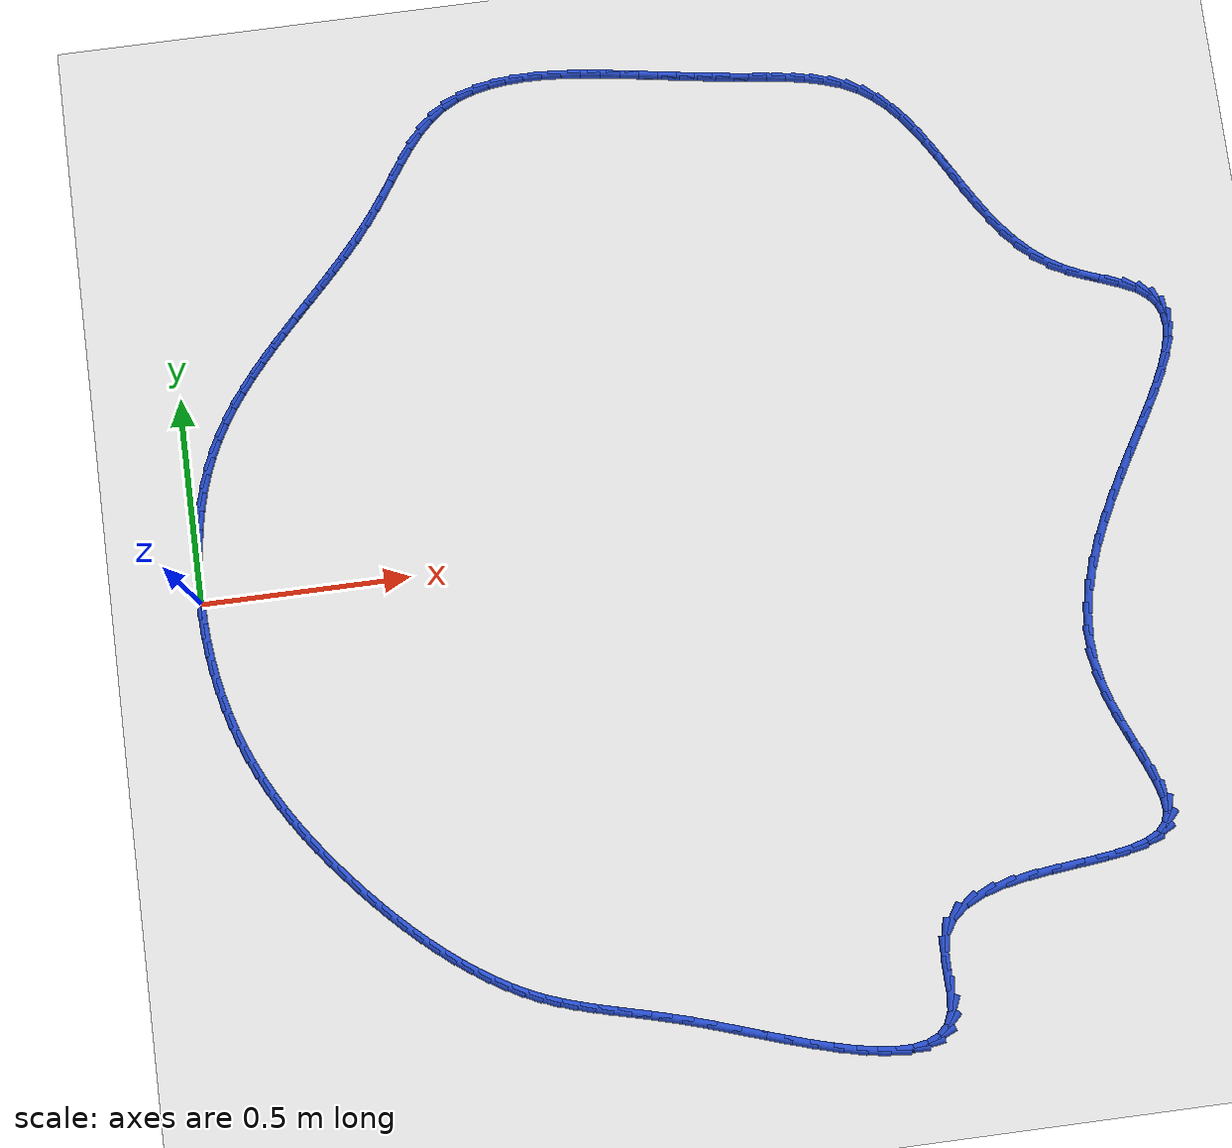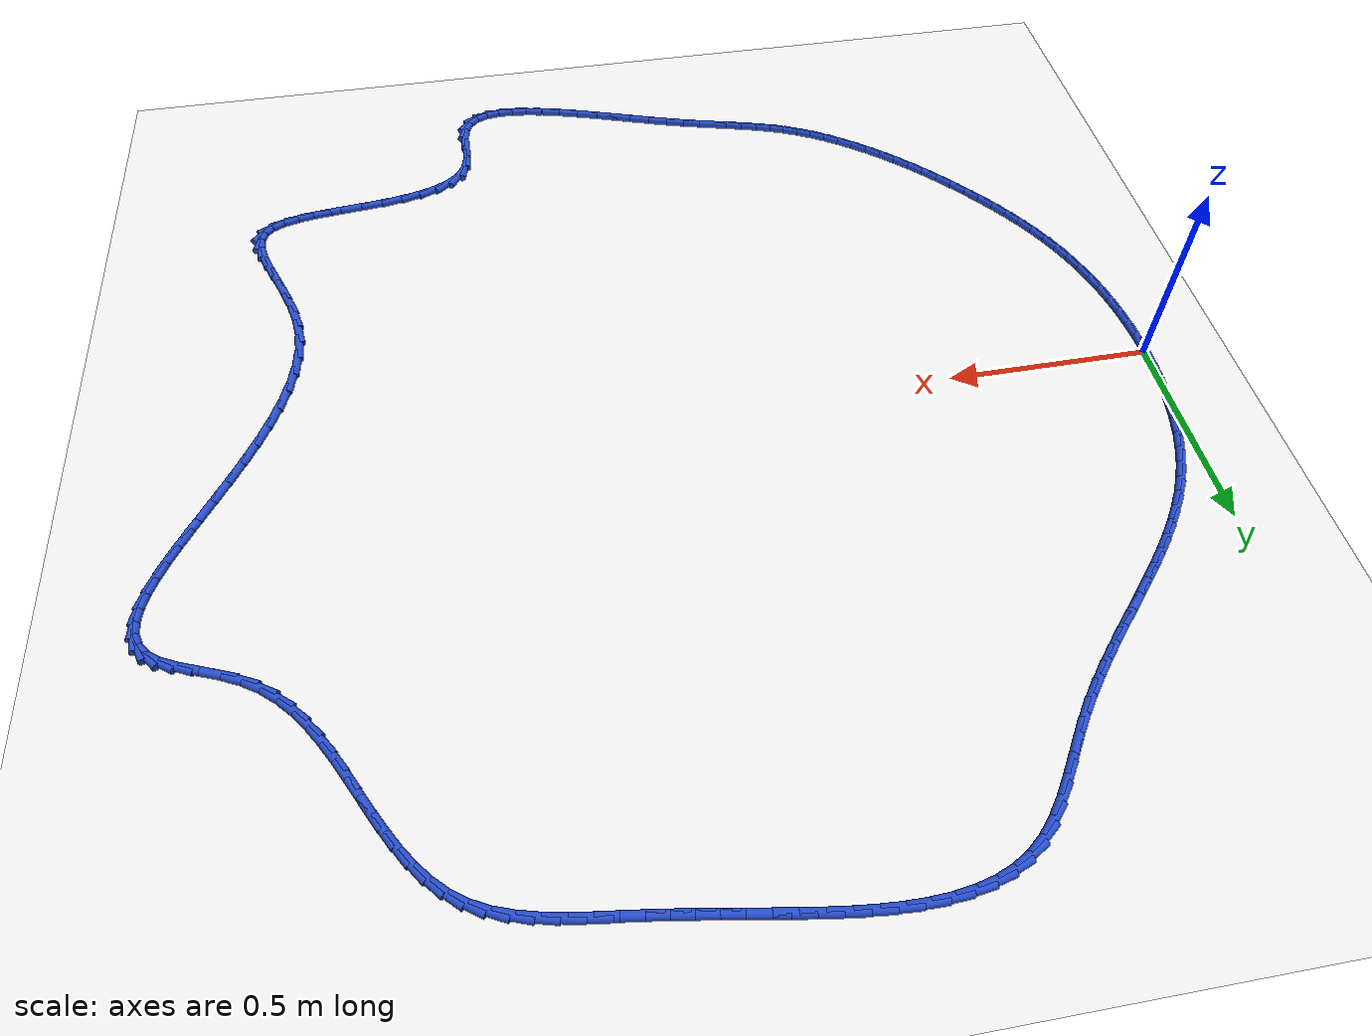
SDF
<sdf version="1.6">
 <world name="default">
  <light name="sun" type="directional">
   <pose>0 0 10 0 -0 0</pose>
   <diffuse>0.8 0.8 0.8 1</diffuse>
   <specular>0.2 0.2 0.2 1</specular>
   <attenuation>
    <range>1000</range>
    <constant>0.9</constant>
    <linear>0.01</linear>
    <quadratic>0.001</quadratic>
   </attenuation>
   <direction>-0.5 0.1 -0.9</direction>
  </light>
  <model name="ground_plane">
   <static>1</static>
   <link name="link">
    <collision name="collision">
     <geometry><plane><normal>0 0 1</normal><size>100 100</size></plane></geometry>
     <surface><friction><ode><mu>100</mu><mu2>50</mu2></ode></friction></surface>
    </collision>
    <visual name="visual">
     <cast_shadows>0</cast_shadows>
     <geometry><plane><normal>0 0 1</normal><size>100 100</size></plane></geometry>
     <material>
      <script><uri>file://media/materials/scripts/gazebo.material</uri><name>Gazebo/WhiteGlow</name></script>
     </material>
    </visual>
   </link>
  </model>
  <gravity>0 0 -9.8</gravity>
  <magnetic_field>6e-06 2.3e-05 -4.2e-05</magnetic_field>
  <atmosphere type="adiabatic"/>
  <physics name="default_physics" default="0" type="ode">
   <max_step_size>0.001</max_step_size>
   <real_time_factor>1</real_time_factor>
   <real_time_update_rate>1000</real_time_update_rate>
  </physics>
  <scene><ambient>0.4 0.4 0.4 1</ambient><background>0.7 0.7 0.7 1</background><shadows>1</shadows></scene>
  <spherical_coordinates>
   <surface_model>EARTH_WGS84</surface_model>
   <latitude_deg>0</latitude_deg>
   <longitude_deg>0</longitude_deg>
   <elevation>0</elevation>
   <heading_deg>0</heading_deg>
  </spherical_coordinates>
  <model name="line">
   <link name="link_0">
    <pose>4.0766001685454967e-17 -5.551115123125783e-17 0.01 0 1.57 1.5599970781237409</pose>
    <collision name="collision">
     <geometry><cylinder><radius>0.01</radius><length>0.08</length></cylinder></geometry>
    </collision>
    <visual name="visual">
     <material>
      <script><name>Gazebo/Blue</name><uri>file://media/materials/scripts/gazebo.material</uri></script>
     </material>
     <geometry><cylinder><radius>0.01</radius><length>0.08</length></cylinder></geometry>
    </visual>
   </link>
   <link name="link_1">
    <pose>0.0004927395699502331 0.04562543467197222 0.01 0 1.57 1.518257264437585</pose>
    <collision name="collision">
     <geometry><cylinder><radius>0.01</radius><length>0.08</length></cylinder></geometry>
    </collision>
    <visual name="visual">
     <material>
      <script><name>Gazebo/Blue</name><uri>file://media/materials/scripts/gazebo.material</uri></script>
     </material>
     <geometry><cylinder><radius>0.01</radius><length>0.08</length></cylinder></geometry>
    </visual>
   </link>
   <link name="link_2">
    <pose>0.0028899708029637514 0.09121104249732984 0.01 0 1.57 1.4738781874758704</pose>
    <collision name="collision">
     <geometry><cylinder><radius>0.01</radius><length>0.08</length></cylinder></geometry>
    </collision>
    <visual name="visual">
     <material>
      <script><name>Gazebo/Blue</name><uri>file://media/materials/scripts/gazebo.material</uri></script>
     </material>
     <geometry><cylinder><radius>0.01</radius><length>0.08</length></cylinder></geometry>
    </visual>
   </link>
   <link name="link_3">
    <pose>0.00729627914929314 0.13653283049259837 0.01 0 1.57 1.4263838987702546</pose>
    <collision name="collision">
     <geometry><cylinder><radius>0.01</radius><length>0.08</length></cylinder></geometry>
    </collision>
    <visual name="visual">
     <material>
      <script><name>Gazebo/Blue</name><uri>file://media/materials/scripts/gazebo.material</uri></script>
     </material>
     <geometry><cylinder><radius>0.01</radius><length>0.08</length></cylinder></geometry>
    </visual>
   </link>
   <link name="link_4">
    <pose>0.013816250059190946 0.18136680567430352 0.01 0 1.57 1.3752803222719931</pose>
    <collision name="collision">
     <geometry><cylinder><radius>0.01</radius><length>0.08</length></cylinder></geometry>
    </collision>
    <visual name="visual">
     <material>
      <script><name>Gazebo/Blue</name><uri>file://media/materials/scripts/gazebo.material</uri></script>
     </material>
     <geometry><cylinder><radius>0.01</radius><length>0.08</length></cylinder></geometry>
    </visual>
   </link>
   <link name="link_5">
    <pose>0.02255446898290972 0.22548897505897092 0.01 0 1.57 1.320062551266252</pose>
    <collision name="collision">
     <geometry><cylinder><radius>0.01</radius><length>0.08</length></cylinder></geometry>
    </collision>
    <visual name="visual">
     <material>
      <script><name>Gazebo/Blue</name><uri>file://media/materials/scripts/gazebo.material</uri></script>
     </material>
     <geometry><cylinder><radius>0.01</radius><length>0.08</length></cylinder></geometry>
    </visual>
   </link>
   <link name="link_6">
    <pose>0.03361552137070199 0.26867534566312606 0.01 0 1.57 1.2602309832166376</pose>
    <collision name="collision">
     <geometry><cylinder><radius>0.01</radius><length>0.08</length></cylinder></geometry>
    </collision>
    <visual name="visual">
     <material>
      <script><name>Gazebo/Blue</name><uri>file://media/materials/scripts/gazebo.material</uri></script>
     </material>
     <geometry><cylinder><radius>0.01</radius><length>0.08</length></cylinder></geometry>
    </visual>
   </link>
   <link name="link_7">
    <pose>0.04710399267282034 0.31070192450329465 0.01 0 1.57 1.1953193869684806</pose>
    <collision name="collision">
     <geometry><cylinder><radius>0.01</radius><length>0.08</length></cylinder></geometry>
    </collision>
    <visual name="visual">
     <material>
      <script><name>Gazebo/Blue</name><uri>file://media/materials/scripts/gazebo.material</uri></script>
     </material>
     <geometry><cylinder><radius>0.01</radius><length>0.08</length></cylinder></geometry>
    </visual>
   </link>
   <link name="link_8">
    <pose>0.06312446833951726 0.35134471859600236 0.01 0 1.57 1.1257652403895446</pose>
    <collision name="collision">
     <geometry><cylinder><radius>0.01</radius><length>0.08</length></cylinder></geometry>
    </collision>
    <visual name="visual">
     <material>
      <script><name>Gazebo/Blue</name><uri>file://media/materials/scripts/gazebo.material</uri></script>
     </material>
     <geometry><cylinder><radius>0.01</radius><length>0.08</length></cylinder></geometry>
    </visual>
   </link>
   <link name="link_9">
    <pose>0.0817559265369225 0.3904091851299864 0.01 0 1.57 1.058842065183489</pose>
    <collision name="collision">
     <geometry><cylinder><radius>0.01</radius><length>0.08</length></cylinder></geometry>
    </collision>
    <visual name="visual">
     <material>
      <script><name>Gazebo/Blue</name><uri>file://media/materials/scripts/gazebo.material</uri></script>
     </material>
     <geometry><cylinder><radius>0.01</radius><length>0.08</length></cylinder></geometry>
    </visual>
   </link>
   <link name="link_10">
    <pose>0.10285486777474098 0.42795664619803014 0.01 0 1.57 0.9990269123278682</pose>
    <collision name="collision">
     <geometry><cylinder><radius>0.01</radius><length>0.08</length></cylinder></geometry>
    </collision>
    <visual name="visual">
     <material>
      <script><name>Gazebo/Blue</name><uri>file://media/materials/scripts/gazebo.material</uri></script>
     </material>
     <geometry><cylinder><radius>0.01</radius><length>0.08</length></cylinder></geometry>
    </visual>
   </link>
   <link name="link_11">
    <pose>0.12616340980485868 0.46417997208442524 0.01 0 1.57 0.9469185855319321</pose>
    <collision name="collision">
     <geometry><cylinder><radius>0.01</radius><length>0.08</length></cylinder></geometry>
    </collision>
    <visual name="visual">
     <material>
      <script><name>Gazebo/Blue</name><uri>file://media/materials/scripts/gazebo.material</uri></script>
     </material>
     <geometry><cylinder><radius>0.01</radius><length>0.08</length></cylinder></geometry>
    </visual>
   </link>
   <link name="link_12">
    <pose>0.15142273011574314 0.4992731144423229 0.01 0 1.57 0.9027721931222819</pose>
    <collision name="collision">
     <geometry><cylinder><radius>0.01</radius><length>0.08</length></cylinder></geometry>
    </collision>
    <visual name="visual">
     <material>
      <script><name>Gazebo/Blue</name><uri>file://media/materials/scripts/gazebo.material</uri></script>
     </material>
     <geometry><cylinder><radius>0.01</radius><length>0.08</length></cylinder></geometry>
    </visual>
   </link>
   <link name="link_13">
    <pose>0.17837400619586158 0.5334300249248736 0.01 0 1.57 0.8666155394232734</pose>
    <collision name="collision">
     <geometry><cylinder><radius>0.01</radius><length>0.08</length></cylinder></geometry>
    </collision>
    <visual name="visual">
     <material>
      <script><name>Gazebo/Blue</name><uri>file://media/materials/scripts/gazebo.material</uri></script>
     </material>
     <geometry><cylinder><radius>0.01</radius><length>0.08</length></cylinder></geometry>
    </visual>
   </link>
   <link name="link_14">
    <pose>0.20675841553368132 0.5668446551852275 0.01 0 1.57 0.8383335326738679</pose>
    <collision name="collision">
     <geometry><cylinder><radius>0.01</radius><length>0.08</length></cylinder></geometry>
    </collision>
    <visual name="visual">
     <material>
      <script><name>Gazebo/Blue</name><uri>file://media/materials/scripts/gazebo.material</uri></script>
     </material>
     <geometry><cylinder><radius>0.01</radius><length>0.08</length></cylinder></geometry>
    </visual>
   </link>
   <link name="link_15">
    <pose>0.23631713561766995 0.5997109568765362 0.01 0 1.57 0.8177387101790301</pose>
    <collision name="collision">
     <geometry><cylinder><radius>0.01</radius><length>0.08</length></cylinder></geometry>
    </collision>
    <visual name="visual">
     <material>
      <script><name>Gazebo/Blue</name><uri>file://media/materials/scripts/gazebo.material</uri></script>
     </material>
     <geometry><cylinder><radius>0.01</radius><length>0.08</length></cylinder></geometry>
    </visual>
   </link>
   <link name="link_16">
    <pose>0.26679134393629467 0.6322228816519498 0.01 0 1.57 0.8046235800142252</pose>
    <collision name="collision">
     <geometry><cylinder><radius>0.01</radius><length>0.08</length></cylinder></geometry>
    </collision>
    <visual name="visual">
     <material>
      <script><name>Gazebo/Blue</name><uri>file://media/materials/scripts/gazebo.material</uri></script>
     </material>
     <geometry><cylinder><radius>0.01</radius><length>0.08</length></cylinder></geometry>
    </visual>
   </link>
   <link name="link_17">
    <pose>0.29792221797802304 0.6645743811646193 0.01 0 1.57 0.7987952416516418</pose>
    <collision name="collision">
     <geometry><cylinder><radius>0.01</radius><length>0.08</length></cylinder></geometry>
    </collision>
    <visual name="visual">
     <material>
      <script><name>Gazebo/Blue</name><uri>file://media/materials/scripts/gazebo.material</uri></script>
     </material>
     <geometry><cylinder><radius>0.01</radius><length>0.08</length></cylinder></geometry>
    </visual>
   </link>
   <link name="link_18">
    <pose>0.3294509352313222 0.6969594070676949 0.01 0 1.57 0.8000947162542933</pose>
    <collision name="collision">
     <geometry><cylinder><radius>0.01</radius><length>0.08</length></cylinder></geometry>
    </collision>
    <visual name="visual">
     <material>
      <script><name>Gazebo/Blue</name><uri>file://media/materials/scripts/gazebo.material</uri></script>
     </material>
     <geometry><cylinder><radius>0.01</radius><length>0.08</length></cylinder></geometry>
    </visual>
   </link>
   <link name="link_19">
    <pose>0.3611186731846596 0.7295719110143276 0.01 0 1.57 0.8084036189838907</pose>
    <collision name="collision">
     <geometry><cylinder><radius>0.01</radius><length>0.08</length></cylinder></geometry>
    </collision>
    <visual name="visual">
     <material>
      <script><name>Gazebo/Blue</name><uri>file://media/materials/scripts/gazebo.material</uri></script>
     </material>
     <geometry><cylinder><radius>0.01</radius><length>0.08</length></cylinder></geometry>
    </visual>
   </link>
   <link name="link_20">
    <pose>0.39266660932650294 0.7626058446576682 0.01 0 1.57 0.8236401660063645</pose>
    <collision name="collision">
     <geometry><cylinder><radius>0.01</radius><length>0.08</length></cylinder></geometry>
    </collision>
    <visual name="visual">
     <material>
      <script><name>Gazebo/Blue</name><uri>file://media/materials/scripts/gazebo.material</uri></script>
     </material>
     <geometry><cylinder><radius>0.01</radius><length>0.08</length></cylinder></geometry>
    </visual>
   </link>
   <link name="link_21">
    <pose>0.42383592114531915 0.7962551596508674 0.01 0 1.57 0.8457456632771132</pose>
    <collision name="collision">
     <geometry><cylinder><radius>0.01</radius><length>0.08</length></cylinder></geometry>
    </collision>
    <visual name="visual">
     <material>
      <script><name>Gazebo/Blue</name><uri>file://media/materials/scripts/gazebo.material</uri></script>
     </material>
     <geometry><cylinder><radius>0.01</radius><length>0.08</length></cylinder></geometry>
    </visual>
   </link>
   <link name="link_22">
    <pose>0.4543677861295757 0.8307138076470753 0.01 0 1.57 0.8746619823495427</pose>
    <collision name="collision">
     <geometry><cylinder><radius>0.01</radius><length>0.08</length></cylinder></geometry>
    </collision>
    <visual name="visual">
     <material>
      <script><name>Gazebo/Blue</name><uri>file://media/materials/scripts/gazebo.material</uri></script>
     </material>
     <geometry><cylinder><radius>0.01</radius><length>0.08</length></cylinder></geometry>
    </visual>
   </link>
   <link name="link_23">
    <pose>0.48400338176774016 0.8661757402994432 0.01 0 1.57 0.9103003917268055</pose>
    <collision name="collision">
     <geometry><cylinder><radius>0.01</radius><length>0.08</length></cylinder></geometry>
    </collision>
    <visual name="visual">
     <material>
      <script><name>Gazebo/Blue</name><uri>file://media/materials/scripts/gazebo.material</uri></script>
     </material>
     <geometry><cylinder><radius>0.01</radius><length>0.08</length></cylinder></geometry>
    </visual>
   </link>
   <link name="link_24">
    <pose>0.5124838855482798 0.9028349092611215 0.01 0 1.57 0.9509943058661481</pose>
    <collision name="collision">
     <geometry><cylinder><radius>0.01</radius><length>0.08</length></cylinder></geometry>
    </collision>
    <visual name="visual">
     <material>
      <script><name>Gazebo/Blue</name><uri>file://media/materials/scripts/gazebo.material</uri></script>
     </material>
     <geometry><cylinder><radius>0.01</radius><length>0.08</length></cylinder></geometry>
    </visual>
   </link>
   <link name="link_25">
    <pose>0.5395960091554868 0.9408278147379704 0.01 0 1.57 0.9770967797968013</pose>
    <collision name="collision">
     <geometry><cylinder><radius>0.01</radius><length>0.08</length></cylinder></geometry>
    </collision>
    <visual name="visual">
     <material>
      <script><name>Gazebo/Blue</name><uri>file://media/materials/scripts/gazebo.material</uri></script>
     </material>
     <geometry><cylinder><radius>0.01</radius><length>0.08</length></cylinder></geometry>
    </visual>
   </link>
   <link name="link_26">
    <pose>0.5657228701153659 0.9795384592106015 0.01 0 1.57 0.9752075556604449</pose>
    <collision name="collision">
     <geometry><cylinder><radius>0.01</radius><length>0.08</length></cylinder></geometry>
    </collision>
    <visual name="visual">
     <material>
      <script><name>Gazebo/Blue</name><uri>file://media/materials/scripts/gazebo.material</uri></script>
     </material>
     <geometry><cylinder><radius>0.01</radius><length>0.08</length></cylinder></geometry>
    </visual>
   </link>
   <link name="link_27">
    <pose>0.59166680873417 1.01782190300909 0.01 0 1.57 0.9441252896394173</pose>
    <collision name="collision">
     <geometry><cylinder><radius>0.01</radius><length>0.08</length></cylinder></geometry>
    </collision>
    <visual name="visual">
     <material>
      <script><name>Gazebo/Blue</name><uri>file://media/materials/scripts/gazebo.material</uri></script>
     </material>
     <geometry><cylinder><radius>0.01</radius><length>0.08</length></cylinder></geometry>
    </visual>
   </link>
   <link name="link_28">
    <pose>0.6182388766436759 1.0545222152018854 0.01 0 1.57 0.881115119819073</pose>
    <collision name="collision">
     <geometry><cylinder><radius>0.01</radius><length>0.08</length></cylinder></geometry>
    </collision>
    <visual name="visual">
     <material>
      <script><name>Gazebo/Blue</name><uri>file://media/materials/scripts/gazebo.material</uri></script>
     </material>
     <geometry><cylinder><radius>0.01</radius><length>0.08</length></cylinder></geometry>
    </visual>
   </link>
   <link name="link_29">
    <pose>0.6462501254756609 1.0884834648574377 0.01 0 1.57 0.7821620977689119</pose>
    <collision name="collision">
     <geometry><cylinder><radius>0.01</radius><length>0.08</length></cylinder></geometry>
    </collision>
    <visual name="visual">
     <material>
      <script><name>Gazebo/Blue</name><uri>file://media/materials/scripts/gazebo.material</uri></script>
     </material>
     <geometry><cylinder><radius>0.01</radius><length>0.08</length></cylinder></geometry>
    </visual>
   </link>
   <link name="link_30">
    <pose>0.6765116068619019 1.118549721044197 0.01 0 1.57 0.6440983878873386</pose>
    <collision name="collision">
     <geometry><cylinder><radius>0.01</radius><length>0.08</length></cylinder></geometry>
    </collision>
    <visual name="visual">
     <material>
      <script><name>Gazebo/Blue</name><uri>file://media/materials/scripts/gazebo.material</uri></script>
     </material>
     <geometry><cylinder><radius>0.01</radius><length>0.08</length></cylinder></geometry>
    </visual>
   </link>
   <link name="link_31">
    <pose>0.7098305875019284 1.1435700653549248 0.01 0 1.57 0.4850008331735818</pose>
    <collision name="collision">
     <geometry><cylinder><radius>0.01</radius><length>0.08</length></cylinder></geometry>
    </collision>
    <visual name="visual">
     <material>
      <script><name>Gazebo/Blue</name><uri>file://media/materials/scripts/gazebo.material</uri></script>
     </material>
     <geometry><cylinder><radius>0.01</radius><length>0.08</length></cylinder></geometry>
    </visual>
   </link>
   <link name="link_32">
    <pose>0.7465974881838625 1.1629456236803184 0.01 0 1.57 0.3420349609793625</pose>
    <collision name="collision">
     <geometry><cylinder><radius>0.01</radius><length>0.08</length></cylinder></geometry>
    </collision>
    <visual name="visual">
     <material>
      <script><name>Gazebo/Blue</name><uri>file://media/materials/scripts/gazebo.material</uri></script>
     </material>
     <geometry><cylinder><radius>0.01</radius><length>0.08</length></cylinder></geometry>
    </visual>
   </link>
   <link name="link_33">
    <pose>0.7864143831079319 1.1771215581526049 0.01 0 1.57 0.2213549687286205</pose>
    <collision name="collision">
     <geometry><cylinder><radius>0.01</radius><length>0.08</length></cylinder></geometry>
    </collision>
    <visual name="visual">
     <material>
      <script><name>Gazebo/Blue</name><uri>file://media/materials/scripts/gazebo.material</uri></script>
     </material>
     <geometry><cylinder><radius>0.01</radius><length>0.08</length></cylinder></geometry>
    </visual>
   </link>
   <link name="link_34">
    <pose>0.8287956647312638 1.186659151045742 0.01 0 1.57 0.12220682848351921</pose>
    <collision name="collision">
     <geometry><cylinder><radius>0.01</radius><length>0.08</length></cylinder></geometry>
    </collision>
    <visual name="visual">
     <material>
      <script><name>Gazebo/Blue</name><uri>file://media/materials/scripts/gazebo.material</uri></script>
     </material>
     <geometry><cylinder><radius>0.01</radius><length>0.08</length></cylinder></geometry>
    </visual>
   </link>
   <link name="link_35">
    <pose>0.8732557255109842 1.1921196846336868 0.01 0 1.57 0.04220337423758612</pose>
    <collision name="collision">
     <geometry><cylinder><radius>0.01</radius><length>0.08</length></cylinder></geometry>
    </collision>
    <visual name="visual">
     <material>
      <script><name>Gazebo/Blue</name><uri>file://media/materials/scripts/gazebo.material</uri></script>
     </material>
     <geometry><cylinder><radius>0.01</radius><length>0.08</length></cylinder></geometry>
    </visual>
   </link>
   <link name="link_36">
    <pose>0.9193089579042201 1.194064441190396 0.01 0 1.57 -0.02140727101514247</pose>
    <collision name="collision">
     <geometry><cylinder><radius>0.01</radius><length>0.08</length></cylinder></geometry>
    </collision>
    <visual name="visual">
     <material>
      <script><name>Gazebo/Blue</name><uri>file://media/materials/scripts/gazebo.material</uri></script>
     </material>
     <geometry><cylinder><radius>0.01</radius><length>0.08</length></cylinder></geometry>
    </visual>
   </link>
   <link name="link_37">
    <pose>0.9664697543680985 1.193054702989828 0.01 0 1.57 -0.0710970966772412</pose>
    <collision name="collision">
     <geometry><cylinder><radius>0.01</radius><length>0.08</length></cylinder></geometry>
    </collision>
    <visual name="visual">
     <material>
      <script><name>Gazebo/Blue</name><uri>file://media/materials/scripts/gazebo.material</uri></script>
     </material>
     <geometry><cylinder><radius>0.01</radius><length>0.08</length></cylinder></geometry>
    </visual>
   </link>
   <link name="link_38">
    <pose>1.0142525073597453 1.1896517523059391 0.01 0 1.57 -0.10881263816509414</pose>
    <collision name="collision">
     <geometry><cylinder><radius>0.01</radius><length>0.08</length></cylinder></geometry>
    </collision>
    <visual name="visual">
     <material>
      <script><name>Gazebo/Blue</name><uri>file://media/materials/scripts/gazebo.material</uri></script>
     </material>
     <geometry><cylinder><radius>0.01</radius><length>0.08</length></cylinder></geometry>
    </visual>
   </link>
   <link name="link_39">
    <pose>1.0621716093362874 1.184416871412687 0.01 0 1.57 -0.13591428378970402</pose>
    <collision name="collision">
     <geometry><cylinder><radius>0.01</radius><length>0.08</length></cylinder></geometry>
    </collision>
    <visual name="visual">
     <material>
      <script><name>Gazebo/Blue</name><uri>file://media/materials/scripts/gazebo.material</uri></script>
     </material>
     <geometry><cylinder><radius>0.01</radius><length>0.08</length></cylinder></geometry>
    </visual>
   </link>
   <link name="link_40">
    <pose>1.1097414527548515 1.177911342584029 0.01 0 1.57 -0.15316971710238506</pose>
    <collision name="collision">
     <geometry><cylinder><radius>0.01</radius><length>0.08</length></cylinder></geometry>
    </collision>
    <visual name="visual">
     <material>
      <script><name>Gazebo/Blue</name><uri>file://media/materials/scripts/gazebo.material</uri></script>
     </material>
     <geometry><cylinder><radius>0.01</radius><length>0.08</length></cylinder></geometry>
    </visual>
   </link>
   <link name="link_41">
    <pose>1.156476430072564 1.1706964480939228 0.01 0 1.57 -0.16119935876349228</pose>
    <collision name="collision">
     <geometry><cylinder><radius>0.01</radius><length>0.08</length></cylinder></geometry>
    </collision>
    <visual name="visual">
     <material>
      <script><name>Gazebo/Blue</name><uri>file://media/materials/scripts/gazebo.material</uri></script>
     </material>
     <geometry><cylinder><radius>0.01</radius><length>0.08</length></cylinder></geometry>
    </visual>
   </link>
   <link name="link_42">
    <pose>1.2019497395227572 1.1633020198925648 0.01 0 1.57 -0.1640356536661924</pose>
    <collision name="collision">
     <geometry><cylinder><radius>0.01</radius><length>0.08</length></cylinder></geometry>
    </collision>
    <visual name="visual">
     <material>
      <script><name>Gazebo/Blue</name><uri>file://media/materials/scripts/gazebo.material</uri></script>
     </material>
     <geometry><cylinder><radius>0.01</radius><length>0.08</length></cylinder></geometry>
    </visual>
   </link>
   <link name="link_43">
    <pose>1.2462849953902118 1.1559635181160608 0.01 0 1.57 -0.16375785305083437</pose>
    <collision name="collision">
     <geometry><cylinder><radius>0.01</radius><length>0.08</length></cylinder></geometry>
    </collision>
    <visual name="visual">
     <material>
      <script><name>Gazebo/Blue</name><uri>file://media/materials/scripts/gazebo.material</uri></script>
     </material>
     <geometry><cylinder><radius>0.01</radius><length>0.08</length></cylinder></geometry>
    </visual>
   </link>
   <link name="link_44">
    <pose>1.2899064507237932 1.1487556162044548 0.01 0 1.57 -0.16024483841536052</pose>
    <collision name="collision">
     <geometry><cylinder><radius>0.01</radius><length>0.08</length></cylinder></geometry>
    </collision>
    <visual name="visual">
     <material>
      <script><name>Gazebo/Blue</name><uri>file://media/materials/scripts/gazebo.material</uri></script>
     </material>
     <geometry><cylinder><radius>0.01</radius><length>0.08</length></cylinder></geometry>
    </visual>
   </link>
   <link name="link_45">
    <pose>1.3332414062798958 1.1417513576322567 0.01 0 1.57 -0.1535253820327111</pose>
    <collision name="collision">
     <geometry><cylinder><radius>0.01</radius><length>0.08</length></cylinder></geometry>
    </collision>
    <visual name="visual">
     <material>
      <script><name>Gazebo/Blue</name><uri>file://media/materials/scripts/gazebo.material</uri></script>
     </material>
     <geometry><cylinder><radius>0.01</radius><length>0.08</length></cylinder></geometry>
    </visual>
   </link>
   <link name="link_46">
    <pose>1.376717162814913 1.1350237858739776 0.01 0 1.57 -0.14380700129850343</pose>
    <collision name="collision">
     <geometry><cylinder><radius>0.01</radius><length>0.08</length></cylinder></geometry>
    </collision>
    <visual name="visual">
     <material>
      <script><name>Gazebo/Blue</name><uri>file://media/materials/scripts/gazebo.material</uri></script>
     </material>
     <geometry><cylinder><radius>0.01</radius><length>0.08</length></cylinder></geometry>
    </visual>
   </link>
   <link name="link_47">
    <pose>1.4207610210852377 1.1286459444041266 0.01 0 1.57 -0.13222648996017403</pose>
    <collision name="collision">
     <geometry><cylinder><radius>0.01</radius><length>0.08</length></cylinder></geometry>
    </collision>
    <visual name="visual">
     <material>
      <script><name>Gazebo/Blue</name><uri>file://media/materials/scripts/gazebo.material</uri></script>
     </material>
     <geometry><cylinder><radius>0.01</radius><length>0.08</length></cylinder></geometry>
    </visual>
   </link>
   <link name="link_48">
    <pose>1.4657611575061533 1.1226608125541793 0.01 0 1.57 -0.13117452939009133</pose>
    <collision name="collision">
     <geometry><cylinder><radius>0.01</radius><length>0.08</length></cylinder></geometry>
    </collision>
    <visual name="visual">
     <material>
      <script><name>Gazebo/Blue</name><uri>file://media/materials/scripts/gazebo.material</uri></script>
     </material>
     <geometry><cylinder><radius>0.01</radius><length>0.08</length></cylinder></geometry>
    </visual>
   </link>
   <link name="link_49">
    <pose>1.5114783349005732 1.116629249025633 0.01 0 1.57 -0.15000429552780856</pose>
    <collision name="collision">
     <geometry><cylinder><radius>0.01</radius><length>0.08</length></cylinder></geometry>
    </collision>
    <visual name="visual">
     <material>
      <script><name>Gazebo/Blue</name><uri>file://media/materials/scripts/gazebo.material</uri></script>
     </material>
     <geometry><cylinder><radius>0.01</radius><length>0.08</length></cylinder></geometry>
    </visual>
   </link>
   <link name="link_50">
    <pose>1.5571679087123893 1.1097237445806671 0.01 0 1.57 -0.18961904936485577</pose>
    <collision name="collision">
     <geometry><cylinder><radius>0.01</radius><length>0.08</length></cylinder></geometry>
    </collision>
    <visual name="visual">
     <material>
      <script><name>Gazebo/Blue</name><uri>file://media/materials/scripts/gazebo.material</uri></script>
     </material>
     <geometry><cylinder><radius>0.01</radius><length>0.08</length></cylinder></geometry>
    </visual>
   </link>
   <link name="link_51">
    <pose>1.602070869524743 1.1011057516555496 0.01 0 1.57 -0.25212257753629713</pose>
    <collision name="collision">
     <geometry><cylinder><radius>0.01</radius><length>0.08</length></cylinder></geometry>
    </collision>
    <visual name="visual">
     <material>
      <script><name>Gazebo/Blue</name><uri>file://media/materials/scripts/gazebo.material</uri></script>
     </material>
     <geometry><cylinder><radius>0.01</radius><length>0.08</length></cylinder></geometry>
    </visual>
   </link>
   <link name="link_52">
    <pose>1.6454282079207743 1.0899367226865457 0.01 0 1.57 -0.34079554602121986</pose>
    <collision name="collision">
     <geometry><cylinder><radius>0.01</radius><length>0.08</length></cylinder></geometry>
    </collision>
    <visual name="visual">
     <material>
      <script><name>Gazebo/Blue</name><uri>file://media/materials/scripts/gazebo.material</uri></script>
     </material>
     <geometry><cylinder><radius>0.01</radius><length>0.08</length></cylinder></geometry>
    </visual>
   </link>
   <link name="link_53">
    <pose>1.6864809144836244 1.0753781101099233 0.01 0 1.57 -0.45926227998942915</pose>
    <collision name="collision">
     <geometry><cylinder><radius>0.01</radius><length>0.08</length></cylinder></geometry>
    </collision>
    <visual name="visual">
     <material>
      <script><name>Gazebo/Blue</name><uri>file://media/materials/scripts/gazebo.material</uri></script>
     </material>
     <geometry><cylinder><radius>0.01</radius><length>0.08</length></cylinder></geometry>
    </visual>
   </link>
   <link name="link_54">
    <pose>1.7244699797964345 1.0565913663619488 0.01 0 1.57 -0.6023628784856525</pose>
    <collision name="collision">
     <geometry><cylinder><radius>0.01</radius><length>0.08</length></cylinder></geometry>
    </collision>
    <visual name="visual">
     <material>
      <script><name>Gazebo/Blue</name><uri>file://media/materials/scripts/gazebo.material</uri></script>
     </material>
     <geometry><cylinder><radius>0.01</radius><length>0.08</length></cylinder></geometry>
    </visual>
   </link>
   <link name="link_55">
    <pose>1.758833281919285 1.032962773614327 0.01 0 1.57 -0.7350517453892694</pose>
    <collision name="collision">
     <geometry><cylinder><radius>0.01</radius><length>0.08</length></cylinder></geometry>
    </collision>
    <visual name="visual">
     <material>
      <script><name>Gazebo/Blue</name><uri>file://media/materials/scripts/gazebo.material</uri></script>
     </material>
     <geometry><cylinder><radius>0.01</radius><length>0.08</length></cylinder></geometry>
    </visual>
   </link>
   <link name="link_56">
    <pose>1.7898903697625963 1.0048854115614254 0.01 0 1.57 -0.8440696737563672</pose>
    <collision name="collision">
     <geometry><cylinder><radius>0.01</radius><length>0.08</length></cylinder></geometry>
    </collision>
    <visual name="visual">
     <material>
      <script><name>Gazebo/Blue</name><uri>file://media/materials/scripts/gazebo.material</uri></script>
     </material>
     <geometry><cylinder><radius>0.01</radius><length>0.08</length></cylinder></geometry>
    </visual>
   </link>
   <link name="link_57">
    <pose>1.818207485998988 0.9730340644232179 0.01 0 1.57 -0.9285691239250818</pose>
    <collision name="collision">
     <geometry><cylinder><radius>0.01</radius><length>0.08</length></cylinder></geometry>
    </collision>
    <visual name="visual">
     <material>
      <script><name>Gazebo/Blue</name><uri>file://media/materials/scripts/gazebo.material</uri></script>
     </material>
     <geometry><cylinder><radius>0.01</radius><length>0.08</length></cylinder></geometry>
    </visual>
   </link>
   <link name="link_58">
    <pose>1.8443508850422297 0.9380835298271322 0.01 0 1.57 -0.9898783678970184</pose>
    <collision name="collision">
     <geometry><cylinder><radius>0.01</radius><length>0.08</length></cylinder></geometry>
    </collision>
    <visual name="visual">
     <material>
      <script><name>Gazebo/Blue</name><uri>file://media/materials/scripts/gazebo.material</uri></script>
     </material>
     <geometry><cylinder><radius>0.01</radius><length>0.08</length></cylinder></geometry>
    </visual>
   </link>
   <link name="link_59">
    <pose>1.8688868213060892 0.9007086054005956 0.01 0 1.57 -1.0300007008097212</pose>
    <collision name="collision">
     <geometry><cylinder><radius>0.01</radius><length>0.08</length></cylinder></geometry>
    </collision>
    <visual name="visual">
     <material>
      <script><name>Gazebo/Blue</name><uri>file://media/materials/scripts/gazebo.material</uri></script>
     </material>
     <geometry><cylinder><radius>0.01</radius><length>0.08</length></cylinder></geometry>
    </visual>
   </link>
   <link name="link_60">
    <pose>1.8923815492043363 0.8615840887710358 0.01 0 1.57 -1.0507367019457632</pose>
    <collision name="collision">
     <geometry><cylinder><radius>0.01</radius><length>0.08</length></cylinder></geometry>
    </collision>
    <visual name="visual">
     <material>
      <script><name>Gazebo/Blue</name><uri>file://media/materials/scripts/gazebo.material</uri></script>
     </material>
     <geometry><cylinder><radius>0.01</radius><length>0.08</length></cylinder></geometry>
    </visual>
   </link>
   <link name="link_61">
    <pose>1.9154013231507405 0.8213847775658801 0.01 0 1.57 -1.053295582378892</pose>
    <collision name="collision">
     <geometry><cylinder><radius>0.01</radius><length>0.08</length></cylinder></geometry>
    </collision>
    <visual name="visual">
     <material>
      <script><name>Gazebo/Blue</name><uri>file://media/materials/scripts/gazebo.material</uri></script>
     </material>
     <geometry><cylinder><radius>0.01</radius><length>0.08</length></cylinder></geometry>
    </visual>
   </link>
   <link name="link_62">
    <pose>1.9385123975590697 0.7807854694125557 0.01 0 1.57 -1.0381822895705313</pose>
    <collision name="collision">
     <geometry><cylinder><radius>0.01</radius><length>0.08</length></cylinder></geometry>
    </collision>
    <visual name="visual">
     <material>
      <script><name>Gazebo/Blue</name><uri>file://media/materials/scripts/gazebo.material</uri></script>
     </material>
     <geometry><cylinder><radius>0.01</radius><length>0.08</length></cylinder></geometry>
    </visual>
   </link>
   <link name="link_63">
    <pose>1.9622810268430935 0.7404609619384901 0.01 0 1.57 -1.0052306896123775</pose>
    <collision name="collision">
     <geometry><cylinder><radius>0.01</radius><length>0.08</length></cylinder></geometry>
    </collision>
    <visual name="visual">
     <material>
      <script><name>Gazebo/Blue</name><uri>file://media/materials/scripts/gazebo.material</uri></script>
     </material>
     <geometry><cylinder><radius>0.01</radius><length>0.08</length></cylinder></geometry>
    </visual>
   </link>
   <link name="link_64">
    <pose>1.987273465416581 0.7010860527711116 0.01 0 1.57 -0.9537491371853772</pose>
    <collision name="collision">
     <geometry><cylinder><radius>0.01</radius><length>0.08</length></cylinder></geometry>
    </collision>
    <visual name="visual">
     <material>
      <script><name>Gazebo/Blue</name><uri>file://media/materials/scripts/gazebo.material</uri></script>
     </material>
     <geometry><cylinder><radius>0.01</radius><length>0.08</length></cylinder></geometry>
    </visual>
   </link>
   <link name="link_65">
    <pose>2.0140559676933005 0.6633355395378467 0.01 0 1.57 -0.8828203982317435</pose>
    <collision name="collision">
     <geometry><cylinder><radius>0.01</radius><length>0.08</length></cylinder></geometry>
    </collision>
    <visual name="visual">
     <material>
      <script><name>Gazebo/Blue</name><uri>file://media/materials/scripts/gazebo.material</uri></script>
     </material>
     <geometry><cylinder><radius>0.01</radius><length>0.08</length></cylinder></geometry>
    </visual>
   </link>
   <link name="link_66">
    <pose>2.043194788087023 0.627884219866123 0.01 0 1.57 -0.7918428184935988</pose>
    <collision name="collision">
     <geometry><cylinder><radius>0.01</radius><length>0.08</length></cylinder></geometry>
    </collision>
    <visual name="visual">
     <material>
      <script><name>Gazebo/Blue</name><uri>file://media/materials/scripts/gazebo.material</uri></script>
     </material>
     <geometry><cylinder><radius>0.01</radius><length>0.08</length></cylinder></geometry>
    </visual>
   </link>
   <link name="link_67">
    <pose>2.0752561810115147 0.5954068913833682 0.01 0 1.57 -0.6813667376273711</pose>
    <collision name="collision">
     <geometry><cylinder><radius>0.01</radius><length>0.08</length></cylinder></geometry>
    </collision>
    <visual name="visual">
     <material>
      <script><name>Gazebo/Blue</name><uri>file://media/materials/scripts/gazebo.material</uri></script>
     </material>
     <geometry><cylinder><radius>0.01</radius><length>0.08</length></cylinder></geometry>
    </visual>
   </link>
   <link name="link_68">
    <pose>2.1108064008805467 0.5665783517170095 0.01 0 1.57 -0.5540917921333697</pose>
    <collision name="collision">
     <geometry><cylinder><radius>0.01</radius><length>0.08</length></cylinder></geometry>
    </collision>
    <visual name="visual">
     <material>
      <script><name>Gazebo/Blue</name><uri>file://media/materials/scripts/gazebo.material</uri></script>
     </material>
     <geometry><cylinder><radius>0.01</radius><length>0.08</length></cylinder></geometry>
    </visual>
   </link>
   <link name="link_69">
    <pose>2.1504110831496677 0.5420729825750886 0.01 0 1.57 -0.4334395602310649</pose>
    <collision name="collision">
     <geometry><cylinder><radius>0.01</radius><length>0.08</length></cylinder></geometry>
    </collision>
    <visual name="visual">
     <material>
      <script><name>Gazebo/Blue</name><uri>file://media/materials/scripts/gazebo.material</uri></script>
     </material>
     <geometry><cylinder><radius>0.01</radius><length>0.08</length></cylinder></geometry>
    </visual>
   </link>
   <link name="link_70">
    <pose>2.1937907513898356 0.5219972785209317 0.01 0 1.57 -0.3705456879622866</pose>
    <collision name="collision">
     <geometry><cylinder><radius>0.01</radius><length>0.08</length></cylinder></geometry>
    </collision>
    <visual name="visual">
     <material>
      <script><name>Gazebo/Blue</name><uri>file://media/materials/scripts/gazebo.material</uri></script>
     </material>
     <geometry><cylinder><radius>0.01</radius><length>0.08</length></cylinder></geometry>
    </visual>
   </link>
   <link name="link_71">
    <pose>2.2381471645835336 0.5047652078897514 0.01 0 1.57 -0.36941815360986097</pose>
    <collision name="collision">
     <geometry><cylinder><radius>0.01</radius><length>0.08</length></cylinder></geometry>
    </collision>
    <visual name="visual">
     <material>
      <script><name>Gazebo/Blue</name><uri>file://media/materials/scripts/gazebo.material</uri></script>
     </material>
     <geometry><cylinder><radius>0.01</radius><length>0.08</length></cylinder></geometry>
    </visual>
   </link>
   <link name="link_72">
    <pose>2.2802149259553444 0.48847682584818786 0.01 0 1.57 -0.44122542386601443</pose>
    <collision name="collision">
     <geometry><cylinder><radius>0.01</radius><length>0.08</length></cylinder></geometry>
    </collision>
    <visual name="visual">
     <material>
      <script><name>Gazebo/Blue</name><uri>file://media/materials/scripts/gazebo.material</uri></script>
     </material>
     <geometry><cylinder><radius>0.01</radius><length>0.08</length></cylinder></geometry>
    </visual>
   </link>
   <link name="link_73">
    <pose>2.316728638729851 0.47123218756288027 0.01 0 1.57 -0.6219371588305702</pose>
    <collision name="collision">
     <geometry><cylinder><radius>0.01</radius><length>0.08</length></cylinder></geometry>
    </collision>
    <visual name="visual">
     <material>
      <script><name>Gazebo/Blue</name><uri>file://media/materials/scripts/gazebo.material</uri></script>
     </material>
     <geometry><cylinder><radius>0.01</radius><length>0.08</length></cylinder></geometry>
    </visual>
   </link>
   <link name="link_74">
    <pose>2.3446263635961078 0.4512340515643876 0.01 0 1.57 -0.8987083118697661</pose>
    <collision name="collision">
     <geometry><cylinder><radius>0.01</radius><length>0.08</length></cylinder></geometry>
    </collision>
    <visual name="visual">
     <material>
      <script><name>Gazebo/Blue</name><uri>file://media/materials/scripts/gazebo.material</uri></script>
     </material>
     <geometry><cylinder><radius>0.01</radius><length>0.08</length></cylinder></geometry>
    </visual>
   </link>
   <link name="link_75">
    <pose>2.363209620887246 0.4278782279951374 0.01 0 1.57 -1.20745494179985</pose>
    <collision name="collision">
     <geometry><cylinder><radius>0.01</radius><length>0.08</length></cylinder></geometry>
    </collision>
    <visual name="visual">
     <material>
      <script><name>Gazebo/Blue</name><uri>file://media/materials/scripts/gazebo.material</uri></script>
     </material>
     <geometry><cylinder><radius>0.01</radius><length>0.08</length></cylinder></geometry>
    </visual>
   </link>
   <link name="link_76">
    <pose>2.373303920937229 0.40132982243762116 0.01 0 1.57 -1.4879028084055372</pose>
    <collision name="collision">
     <geometry><cylinder><radius>0.01</radius><length>0.08</length></cylinder></geometry>
    </collision>
    <visual name="visual">
     <material>
      <script><name>Gazebo/Blue</name><uri>file://media/materials/scripts/gazebo.material</uri></script>
     </material>
     <geometry><cylinder><radius>0.01</radius><length>0.08</length></cylinder></geometry>
    </visual>
   </link>
   <link name="link_77">
    <pose>2.3757601369782675 0.37176674342051685 0.01 0 1.57 1.4379107605141843</pose>
    <collision name="collision">
     <geometry><cylinder><radius>0.01</radius><length>0.08</length></cylinder></geometry>
    </collision>
    <visual name="visual">
     <material>
      <script><name>Gazebo/Blue</name><uri>file://media/materials/scripts/gazebo.material</uri></script>
     </material>
     <geometry><cylinder><radius>0.01</radius><length>0.08</length></cylinder></geometry>
    </visual>
   </link>
   <link name="link_78">
    <pose>2.3714291422425764 0.3393668994725041 0.01 0 1.57 1.2859017098346563</pose>
    <collision name="collision">
     <geometry><cylinder><radius>0.01</radius><length>0.08</length></cylinder></geometry>
    </collision>
    <visual name="visual">
     <material>
      <script><name>Gazebo/Blue</name><uri>file://media/materials/scripts/gazebo.material</uri></script>
     </material>
     <geometry><cylinder><radius>0.01</radius><length>0.08</length></cylinder></geometry>
    </visual>
   </link>
   <link name="link_79">
    <pose>2.3611618099623684 0.30430819912226115 0.01 0 1.57 1.1825764719931966</pose>
    <collision name="collision">
     <geometry><cylinder><radius>0.01</radius><length>0.08</length></cylinder></geometry>
    </collision>
    <visual name="visual">
     <material>
      <script><name>Gazebo/Blue</name><uri>file://media/materials/scripts/gazebo.material</uri></script>
     </material>
     <geometry><cylinder><radius>0.01</radius><length>0.08</length></cylinder></geometry>
    </visual>
   </link>
   <link name="link_80">
    <pose>2.3458090133698546 0.26676855089846707 0.01 0 1.57 1.1138766674025506</pose>
    <collision name="collision">
     <geometry><cylinder><radius>0.01</radius><length>0.08</length></cylinder></geometry>
    </collision>
    <visual name="visual">
     <material>
      <script><name>Gazebo/Blue</name><uri>file://media/materials/scripts/gazebo.material</uri></script>
     </material>
     <geometry><cylinder><radius>0.01</radius><length>0.08</length></cylinder></geometry>
    </visual>
   </link>
   <link name="link_81">
    <pose>2.3262216256972508 0.22692586332980078 0.01 0 1.57 1.069989572174801</pose>
    <collision name="collision">
     <geometry><cylinder><radius>0.01</radius><length>0.08</length></cylinder></geometry>
    </collision>
    <visual name="visual">
     <material>
      <script><name>Gazebo/Blue</name><uri>file://media/materials/scripts/gazebo.material</uri></script>
     </material>
     <geometry><cylinder><radius>0.01</radius><length>0.08</length></cylinder></geometry>
    </visual>
   </link>
   <link name="link_82">
    <pose>2.3032505201767677 0.18495804494494028 0.01 0 1.57 1.044646564025618</pose>
    <collision name="collision">
     <geometry><cylinder><radius>0.01</radius><length>0.08</length></cylinder></geometry>
    </collision>
    <visual name="visual">
     <material>
      <script><name>Gazebo/Blue</name><uri>file://media/materials/scripts/gazebo.material</uri></script>
     </material>
     <geometry><cylinder><radius>0.01</radius><length>0.08</length></cylinder></geometry>
    </visual>
   </link>
   <link name="link_83">
    <pose>2.2777465700406196 0.1410430042725651 0.01 0 1.57 1.0340011005281176</pose>
    <collision name="collision">
     <geometry><cylinder><radius>0.01</radius><length>0.08</length></cylinder></geometry>
    </collision>
    <visual name="visual">
     <material>
      <script><name>Gazebo/Blue</name><uri>file://media/materials/scripts/gazebo.material</uri></script>
     </material>
     <geometry><cylinder><radius>0.01</radius><length>0.08</length></cylinder></geometry>
    </visual>
   </link>
   <link name="link_84">
    <pose>2.250560648521019 0.09535864984135345 0.01 0 1.57 1.0358137838598855</pose>
    <collision name="collision">
     <geometry><cylinder><radius>0.01</radius><length>0.08</length></cylinder></geometry>
    </collision>
    <visual name="visual">
     <material>
      <script><name>Gazebo/Blue</name><uri>file://media/materials/scripts/gazebo.material</uri></script>
     </material>
     <geometry><cylinder><radius>0.01</radius><length>0.08</length></cylinder></geometry>
    </visual>
   </link>
   <link name="link_85">
    <pose>2.222543628850178 0.0480828901799847 0.01 0 1.57 1.0489478130807208</pose>
    <collision name="collision">
     <geometry><cylinder><radius>0.01</radius><length>0.08</length></cylinder></geometry>
    </collision>
    <visual name="visual">
     <material>
      <script><name>Gazebo/Blue</name><uri>file://media/materials/scripts/gazebo.material</uri></script>
     </material>
     <geometry><cylinder><radius>0.01</radius><length>0.08</length></cylinder></geometry>
    </visual>
   </link>
   <link name="link_86">
    <pose>2.1945463842603115 -0.000606366182862722 0.01 0 1.57 1.0730740660798603</pose>
    <collision name="collision">
     <geometry><cylinder><radius>0.01</radius><length>0.08</length></cylinder></geometry>
    </collision>
    <visual name="visual">
     <material>
      <script><name>Gazebo/Blue</name><uri>file://media/materials/scripts/gazebo.material</uri></script>
     </material>
     <geometry><cylinder><radius>0.01</radius><length>0.08</length></cylinder></geometry>
    </visual>
   </link>
   <link name="link_87">
    <pose>2.167419787983631 -0.050531210718510064 0.01 0 1.57 1.1085020541007886</pose>
    <collision name="collision">
     <geometry><cylinder><radius>0.01</radius><length>0.08</length></cylinder></geometry>
    </collision>
    <visual name="visual">
     <material>
      <script><name>Gazebo/Blue</name><uri>file://media/materials/scripts/gazebo.material</uri></script>
     </material>
     <geometry><cylinder><radius>0.01</radius><length>0.08</length></cylinder></geometry>
    </visual>
   </link>
   <link name="link_88">
    <pose>2.1420147132523484 -0.10151373489827858 0.01 0 1.57 1.1560751038383181</pose>
    <collision name="collision">
     <geometry><cylinder><radius>0.01</radius><length>0.08</length></cylinder></geometry>
    </collision>
    <visual name="visual">
     <material>
      <script><name>Gazebo/Blue</name><uri>file://media/materials/scripts/gazebo.material</uri></script>
     </material>
     <geometry><cylinder><radius>0.01</radius><length>0.08</length></cylinder></geometry>
    </visual>
   </link>
   <link name="link_89">
    <pose>2.1191820332986784 -0.15337603019349053 0.01 0 1.57 1.2170746392446472</pose>
    <collision name="collision">
     <geometry><cylinder><radius>0.01</radius><length>0.08</length></cylinder></geometry>
    </collision>
    <visual name="visual">
     <material>
      <script><name>Gazebo/Blue</name><uri>file://media/materials/scripts/gazebo.material</uri></script>
     </material>
     <geometry><cylinder><radius>0.01</radius><length>0.08</length></cylinder></geometry>
    </visual>
   </link>
   <link name="link_90">
    <pose>2.099772621354834 -0.2059401880754652 0.01 0 1.57 1.2930672977358457</pose>
    <collision name="collision">
     <geometry><cylinder><radius>0.01</radius><length>0.08</length></cylinder></geometry>
    </collision>
    <visual name="visual">
     <material>
      <script><name>Gazebo/Blue</name><uri>file://media/materials/scripts/gazebo.material</uri></script>
     </material>
     <geometry><cylinder><radius>0.01</radius><length>0.08</length></cylinder></geometry>
    </visual>
   </link>
   <link name="link_91">
    <pose>2.084637350653027 -0.2590283000155247 0.01 0 1.57 1.3856047342201527</pose>
    <collision name="collision">
     <geometry><cylinder><radius>0.01</radius><length>0.08</length></cylinder></geometry>
    </collision>
    <visual name="visual">
     <material>
      <script><name>Gazebo/Blue</name><uri>file://media/materials/scripts/gazebo.material</uri></script>
     </material>
     <geometry><cylinder><radius>0.01</radius><length>0.08</length></cylinder></geometry>
    </visual>
   </link>
   <link name="link_92">
    <pose>2.0746270944254714 -0.3124624574849904 0.01 0 1.57 1.4956731181866083</pose>
    <collision name="collision">
     <geometry><cylinder><radius>0.01</radius><length>0.08</length></cylinder></geometry>
    </collision>
    <visual name="visual">
     <material>
      <script><name>Gazebo/Blue</name><uri>file://media/materials/scripts/gazebo.material</uri></script>
     </material>
     <geometry><cylinder><radius>0.01</radius><length>0.08</length></cylinder></geometry>
    </visual>
   </link>
   <link name="link_93">
    <pose>2.0705927259043793 -0.3660647519551835 0.01 0 1.57 -1.518739259783545</pose>
    <collision name="collision">
     <geometry><cylinder><radius>0.01</radius><length>0.08</length></cylinder></geometry>
    </collision>
    <visual name="visual">
     <material>
      <script><name>Gazebo/Blue</name><uri>file://media/materials/scripts/gazebo.material</uri></script>
     </material>
     <geometry><cylinder><radius>0.01</radius><length>0.08</length></cylinder></geometry>
    </visual>
   </link>
   <link name="link_94">
    <pose>2.073385118321964 -0.4196572748974262 0.01 0 1.57 -1.3842314266280167</pose>
    <collision name="collision">
     <geometry><cylinder><radius>0.01</radius><length>0.08</length></cylinder></geometry>
    </collision>
    <visual name="visual">
     <material>
      <script><name>Gazebo/Blue</name><uri>file://media/materials/scripts/gazebo.material</uri></script>
     </material>
     <geometry><cylinder><radius>0.01</radius><length>0.08</length></cylinder></geometry>
    </visual>
   </link>
   <link name="link_95">
    <pose>2.083453334374931 -0.4729959848737925 0.01 0 1.57 -1.279418233602411</pose>
    <collision name="collision">
     <geometry><cylinder><radius>0.01</radius><length>0.08</length></cylinder></geometry>
    </collision>
    <visual name="visual">
     <material>
      <script><name>Gazebo/Blue</name><uri>file://media/materials/scripts/gazebo.material</uri></script>
     </material>
     <geometry><cylinder><radius>0.01</radius><length>0.08</length></cylinder></geometry>
    </visual>
   </link>
   <link name="link_96">
    <pose>2.099200044052732 -0.5255000302056368 0.01 0 1.57 -1.2109950455202845</pose>
    <collision name="collision">
     <geometry><cylinder><radius>0.01</radius><length>0.08</length></cylinder></geometry>
    </collision>
    <visual name="visual">
     <material>
      <script><name>Gazebo/Blue</name><uri>file://media/materials/scripts/gazebo.material</uri></script>
     </material>
     <geometry><cylinder><radius>0.01</radius><length>0.08</length></cylinder></geometry>
    </visual>
   </link>
   <link name="link_97">
    <pose>2.1183780889790813 -0.5764816057212141 0.01 0 1.57 -1.175296134099487</pose>
    <collision name="collision">
     <geometry><cylinder><radius>0.01</radius><length>0.08</length></cylinder></geometry>
    </collision>
    <visual name="visual">
     <material>
      <script><name>Gazebo/Blue</name><uri>file://media/materials/scripts/gazebo.material</uri></script>
     </material>
     <geometry><cylinder><radius>0.01</radius><length>0.08</length></cylinder></geometry>
    </visual>
   </link>
   <link name="link_98">
    <pose>2.1387400441845634 -0.6252528623709367 0.01 0 1.57 -1.1725802625752417</pose>
    <collision name="collision">
     <geometry><cylinder><radius>0.01</radius><length>0.08</length></cylinder></geometry>
    </collision>
    <visual name="visual">
     <material>
      <script><name>Gazebo/Blue</name><uri>file://media/materials/scripts/gazebo.material</uri></script>
     </material>
     <geometry><cylinder><radius>0.01</radius><length>0.08</length></cylinder></geometry>
    </visual>
   </link>
   <link name="link_99">
    <pose>2.158038484699765 -0.6711259511052188 0.01 0 1.57 -1.209336298281432</pose>
    <collision name="collision">
     <geometry><cylinder><radius>0.01</radius><length>0.08</length></cylinder></geometry>
    </collision>
    <visual name="visual">
     <material>
      <script><name>Gazebo/Blue</name><uri>file://media/materials/scripts/gazebo.material</uri></script>
     </material>
     <geometry><cylinder><radius>0.01</radius><length>0.08</length></cylinder></geometry>
    </visual>
   </link>
   <link name="link_100">
    <pose>2.1740259855552693 -0.7134130228744712 0.01 0 1.57 -1.3030292994326418</pose>
    <collision name="collision">
     <geometry><cylinder><radius>0.01</radius><length>0.08</length></cylinder></geometry>
    </collision>
    <visual name="visual">
     <material>
      <script><name>Gazebo/Blue</name><uri>file://media/materials/scripts/gazebo.material</uri></script>
     </material>
     <geometry><cylinder><radius>0.01</radius><length>0.08</length></cylinder></geometry>
    </visual>
   </link>
   <link name="link_101">
    <pose>2.184455121781663 -0.7514262286291075 0.01 0 1.57 -1.4915908683314771</pose>
    <collision name="collision">
     <geometry><cylinder><radius>0.01</radius><length>0.08</length></cylinder></geometry>
    </collision>
    <visual name="visual">
     <material>
      <script><name>Gazebo/Blue</name><uri>file://media/materials/scripts/gazebo.material</uri></script>
     </material>
     <geometry><cylinder><radius>0.01</radius><length>0.08</length></cylinder></geometry>
    </visual>
   </link>
   <link name="link_102">
    <pose>2.1870784684095304 -0.7844777193195405 0.01 0 1.57 1.3060185319753976</pose>
    <collision name="collision">
     <geometry><cylinder><radius>0.01</radius><length>0.08</length></cylinder></geometry>
    </collision>
    <visual name="visual">
     <material>
      <script><name>Gazebo/Blue</name><uri>file://media/materials/scripts/gazebo.material</uri></script>
     </material>
     <geometry><cylinder><radius>0.01</radius><length>0.08</length></cylinder></geometry>
    </visual>
   </link>
   <link name="link_103">
    <pose>2.1796486004694566 -0.8118796458961829 0.01 0 1.57 0.8317705952721794</pose>
    <collision name="collision">
     <geometry><cylinder><radius>0.01</radius><length>0.08</length></cylinder></geometry>
    </collision>
    <visual name="visual">
     <material>
      <script><name>Gazebo/Blue</name><uri>file://media/materials/scripts/gazebo.material</uri></script>
     </material>
     <geometry><cylinder><radius>0.01</radius><length>0.08</length></cylinder></geometry>
    </visual>
   </link>
   <link name="link_104">
    <pose>2.1602987668952647 -0.8331127595565482 0.01 0 1.57 0.4771071912038997</pose>
    <collision name="collision">
     <geometry><cylinder><radius>0.01</radius><length>0.08</length></cylinder></geometry>
    </collision>
    <visual name="visual">
     <material>
      <script><name>Gazebo/Blue</name><uri>file://media/materials/scripts/gazebo.material</uri></script>
     </material>
     <geometry><cylinder><radius>0.01</radius><length>0.08</length></cylinder></geometry>
    </visual>
   </link>
   <link name="link_105">
    <pose>2.129854897404962 -0.8488503982284561 0.01 0 1.57 0.28132576874966747</pose>
    <collision name="collision">
     <geometry><cylinder><radius>0.01</radius><length>0.08</length></cylinder></geometry>
    </collision>
    <visual name="visual">
     <material>
      <script><name>Gazebo/Blue</name><uri>file://media/materials/scripts/gazebo.material</uri></script>
     </material>
     <geometry><cylinder><radius>0.01</radius><length>0.08</length></cylinder></geometry>
    </visual>
   </link>
   <link name="link_106">
    <pose>2.09030411192006 -0.8602801902956166 0.01 0 1.57 0.17625983426204944</pose>
    <collision name="collision">
     <geometry><cylinder><radius>0.01</radius><length>0.08</length></cylinder></geometry>
    </collision>
    <visual name="visual">
     <material>
      <script><name>Gazebo/Blue</name><uri>file://media/materials/scripts/gazebo.material</uri></script>
     </material>
     <geometry><cylinder><radius>0.01</radius><length>0.08</length></cylinder></geometry>
    </visual>
   </link>
   <link name="link_107">
    <pose>2.0436380970620003 -0.8685917867304436 0.01 0 1.57 0.12263133509250113</pose>
    <collision name="collision">
     <geometry><cylinder><radius>0.01</radius><length>0.08</length></cylinder></geometry>
    </collision>
    <visual name="visual">
     <material>
      <script><name>Gazebo/Blue</name><uri>file://media/materials/scripts/gazebo.material</uri></script>
     </material>
     <geometry><cylinder><radius>0.01</radius><length>0.08</length></cylinder></geometry>
    </visual>
   </link>
   <link name="link_108">
    <pose>1.991848539452224 -0.8749748385053504 0.01 0 1.57 0.10240838503690754</pose>
    <collision name="collision">
     <geometry><cylinder><radius>0.01</radius><length>0.08</length></cylinder></geometry>
    </collision>
    <visual name="visual">
     <material>
      <script><name>Gazebo/Blue</name><uri>file://media/materials/scripts/gazebo.material</uri></script>
     </material>
     <geometry><cylinder><radius>0.01</radius><length>0.08</length></cylinder></geometry>
    </visual>
   </link>
   <link name="link_109">
    <pose>1.9369271257121725 -0.8806189965927509 0.01 0 1.57 0.10829289213533846</pose>
    <collision name="collision">
     <geometry><cylinder><radius>0.01</radius><length>0.08</length></cylinder></geometry>
    </collision>
    <visual name="visual">
     <material>
      <script><name>Gazebo/Blue</name><uri>file://media/materials/scripts/gazebo.material</uri></script>
     </material>
     <geometry><cylinder><radius>0.01</radius><length>0.08</length></cylinder></geometry>
    </visual>
   </link>
   <link name="link_110">
    <pose>1.880865542463286 -0.8867139119650588 0.01 0 1.57 0.13920100551002376</pose>
    <collision name="collision">
     <geometry><cylinder><radius>0.01</radius><length>0.08</length></cylinder></geometry>
    </collision>
    <visual name="visual">
     <material>
      <script><name>Gazebo/Blue</name><uri>file://media/materials/scripts/gazebo.material</uri></script>
     </material>
     <geometry><cylinder><radius>0.01</radius><length>0.08</length></cylinder></geometry>
    </visual>
   </link>
   <link name="link_111">
    <pose>1.8256554763270074 -0.8944492355946875 0.01 0 1.57 0.1990844437430704</pose>
    <collision name="collision">
     <geometry><cylinder><radius>0.01</radius><length>0.08</length></cylinder></geometry>
    </collision>
    <visual name="visual">
     <material>
      <script><name>Gazebo/Blue</name><uri>file://media/materials/scripts/gazebo.material</uri></script>
     </material>
     <geometry><cylinder><radius>0.01</radius><length>0.08</length></cylinder></geometry>
    </visual>
   </link>
   <link name="link_112">
    <pose>1.773288613924777 -0.9050146184540502 0.01 0 1.57 0.297727510294519</pose>
    <collision name="collision">
     <geometry><cylinder><radius>0.01</radius><length>0.08</length></cylinder></geometry>
    </collision>
    <visual name="visual">
     <material>
      <script><name>Gazebo/Blue</name><uri>file://media/materials/scripts/gazebo.material</uri></script>
     </material>
     <geometry><cylinder><radius>0.01</radius><length>0.08</length></cylinder></geometry>
    </visual>
   </link>
   <link name="link_113">
    <pose>1.7257566418780357 -0.919599711515561 0.01 0 1.57 0.4526161519391164</pose>
    <collision name="collision">
     <geometry><cylinder><radius>0.01</radius><length>0.08</length></cylinder></geometry>
    </collision>
    <visual name="visual">
     <material>
      <script><name>Gazebo/Blue</name><uri>file://media/materials/scripts/gazebo.material</uri></script>
     </material>
     <geometry><cylinder><radius>0.01</radius><length>0.08</length></cylinder></geometry>
    </visual>
   </link>
   <link name="link_114">
    <pose>1.6850512468082244 -0.9393941657516331 0.01 0 1.57 0.687679973335966</pose>
    <collision name="collision">
     <geometry><cylinder><radius>0.01</radius><length>0.08</length></cylinder></geometry>
    </collision>
    <visual name="visual">
     <material>
      <script><name>Gazebo/Blue</name><uri>file://media/materials/scripts/gazebo.material</uri></script>
     </material>
     <geometry><cylinder><radius>0.01</radius><length>0.08</length></cylinder></geometry>
    </visual>
   </link>
   <link name="link_115">
    <pose>1.6531641153367844 -0.9655876321346811 0.01 0 1.57 1.0129775330760804</pose>
    <collision name="collision">
     <geometry><cylinder><radius>0.01</radius><length>0.08</length></cylinder></geometry>
    </collision>
    <visual name="visual">
     <material>
      <script><name>Gazebo/Blue</name><uri>file://media/materials/scripts/gazebo.material</uri></script>
     </material>
     <geometry><cylinder><radius>0.01</radius><length>0.08</length></cylinder></geometry>
    </visual>
   </link>
   <link name="link_116">
    <pose>1.632086934085158 -0.9993697616371175 0.01 0 1.57 1.3605635354170675</pose>
    <collision name="collision">
     <geometry><cylinder><radius>0.01</radius><length>0.08</length></cylinder></geometry>
    </collision>
    <visual name="visual">
     <material>
      <script><name>Gazebo/Blue</name><uri>file://media/materials/scripts/gazebo.material</uri></script>
     </material>
     <geometry><cylinder><radius>0.01</radius><length>0.08</length></cylinder></geometry>
    </visual>
   </link>
   <link name="link_117">
    <pose>1.6231199096495845 -1.041392349122935 0.01 0 1.57 1.553132958315199</pose>
    <collision name="collision">
     <geometry><cylinder><radius>0.01</radius><length>0.08</length></cylinder></geometry>
    </collision>
    <visual name="visual">
     <material>
      <script><name>Gazebo/Blue</name><uri>file://media/materials/scripts/gazebo.material</uri></script>
     </material>
     <geometry><cylinder><radius>0.01</radius><length>0.08</length></cylinder></geometry>
    </visual>
   </link>
   <link name="link_118">
    <pose>1.622292906103181 -1.088207742160149 0.01 0 1.57 -1.5509893236732117</pose>
    <collision name="collision">
     <geometry><cylinder><radius>0.01</radius><length>0.08</length></cylinder></geometry>
    </collision>
    <visual name="visual">
     <material>
      <script><name>Gazebo/Blue</name><uri>file://media/materials/scripts/gazebo.material</uri></script>
     </material>
     <geometry><cylinder><radius>0.01</radius><length>0.08</length></cylinder></geometry>
    </visual>
   </link>
   <link name="link_119">
    <pose>1.623209562321865 -1.1344810898509339 0.01 0 1.57 1.478369526519121</pose>
    <collision name="collision">
     <geometry><cylinder><radius>0.01</radius><length>0.08</length></cylinder></geometry>
    </collision>
    <visual name="visual">
     <material>
      <script><name>Gazebo/Blue</name><uri>file://media/materials/scripts/gazebo.material</uri></script>
     </material>
     <geometry><cylinder><radius>0.01</radius><length>0.08</length></cylinder></geometry>
    </visual>
   </link>
   <link name="link_120">
    <pose>1.6194657076161103 -1.1748718393472153 0.01 0 1.57 1.1739515279514678</pose>
    <collision name="collision">
     <geometry><cylinder><radius>0.01</radius><length>0.08</length></cylinder></geometry>
    </collision>
    <visual name="visual">
     <material>
      <script><name>Gazebo/Blue</name><uri>file://media/materials/scripts/gazebo.material</uri></script>
     </material>
     <geometry><cylinder><radius>0.01</radius><length>0.08</length></cylinder></geometry>
    </visual>
   </link>
   <link name="link_121">
    <pose>1.6065624908761813 -1.205661304169138 0.01 0 1.57 0.7787730716247107</pose>
    <collision name="collision">
     <geometry><cylinder><radius>0.01</radius><length>0.08</length></cylinder></geometry>
    </collision>
    <visual name="visual">
     <material>
      <script><name>Gazebo/Blue</name><uri>file://media/materials/scripts/gazebo.material</uri></script>
     </material>
     <geometry><cylinder><radius>0.01</radius><length>0.08</length></cylinder></geometry>
    </visual>
   </link>
   <link name="link_122">
    <pose>1.5847573084412276 -1.2271794613041704 0.01 0 1.57 0.4179248982721116</pose>
    <collision name="collision">
     <geometry><cylinder><radius>0.01</radius><length>0.08</length></cylinder></geometry>
    </collision>
    <visual name="visual">
     <material>
      <script><name>Gazebo/Blue</name><uri>file://media/materials/scripts/gazebo.material</uri></script>
     </material>
     <geometry><cylinder><radius>0.01</radius><length>0.08</length></cylinder></geometry>
    </visual>
   </link>
   <link name="link_123">
    <pose>1.5550374781728715 -1.240377619290298 0.01 0 1.57 0.1577484402809105</pose>
    <collision name="collision">
     <geometry><cylinder><radius>0.01</radius><length>0.08</length></cylinder></geometry>
    </collision>
    <visual name="visual">
     <material>
      <script><name>Gazebo/Blue</name><uri>file://media/materials/scripts/gazebo.material</uri></script>
     </material>
     <geometry><cylinder><radius>0.01</radius><length>0.08</length></cylinder></geometry>
    </visual>
   </link>
   <link name="link_124">
    <pose>1.5183903179327347 -1.2462070866655048 0.01 0 1.57 -0.01380409456265545</pose>
    <collision name="collision">
     <geometry><cylinder><radius>0.01</radius><length>0.08</length></cylinder></geometry>
    </collision>
    <visual name="visual">
     <material>
      <script><name>Gazebo/Blue</name><uri>file://media/materials/scripts/gazebo.material</uri></script>
     </material>
     <geometry><cylinder><radius>0.01</radius><length>0.08</length></cylinder></geometry>
    </visual>
   </link>
   <link name="link_125">
    <pose>1.4758031455824394 -1.2456191719677758 0.01 0 1.57 -0.12666374246653067</pose>
    <collision name="collision">
     <geometry><cylinder><radius>0.01</radius><length>0.08</length></cylinder></geometry>
    </collision>
    <visual name="visual">
     <material>
      <script><name>Gazebo/Blue</name><uri>file://media/materials/scripts/gazebo.material</uri></script>
     </material>
     <geometry><cylinder><radius>0.01</radius><length>0.08</length></cylinder></geometry>
    </visual>
   </link>
   <link name="link_126">
    <pose>1.428263278983606 -1.2395651837350943 0.01 0 1.57 -0.20238823856352897</pose>
    <collision name="collision">
     <geometry><cylinder><radius>0.01</radius><length>0.08</length></cylinder></geometry>
    </collision>
    <visual name="visual">
     <material>
      <script><name>Gazebo/Blue</name><uri>file://media/materials/scripts/gazebo.material</uri></script>
     </material>
     <geometry><cylinder><radius>0.01</radius><length>0.08</length></cylinder></geometry>
    </visual>
   </link>
   <link name="link_127">
    <pose>1.376758035997859 -1.2289964305054455 0.01 0 1.57 -0.25379292036284984</pose>
    <collision name="collision">
     <geometry><cylinder><radius>0.01</radius><length>0.08</length></cylinder></geometry>
    </collision>
    <visual name="visual">
     <material>
      <script><name>Gazebo/Blue</name><uri>file://media/materials/scripts/gazebo.material</uri></script>
     </material>
     <geometry><cylinder><radius>0.01</radius><length>0.08</length></cylinder></geometry>
    </visual>
   </link>
   <link name="link_128">
    <pose>1.3222747344868189 -1.2148642208168139 0.01 0 1.57 -0.28823951175158025</pose>
    <collision name="collision">
     <geometry><cylinder><radius>0.01</radius><length>0.08</length></cylinder></geometry>
    </collision>
    <visual name="visual">
     <material>
      <script><name>Gazebo/Blue</name><uri>file://media/materials/scripts/gazebo.material</uri></script>
     </material>
     <geometry><cylinder><radius>0.01</radius><length>0.08</length></cylinder></geometry>
    </visual>
   </link>
   <link name="link_129">
    <pose>1.265800692312108 -1.1981198632071832 0.01 0 1.57 -0.30989875900197233</pose>
    <collision name="collision">
     <geometry><cylinder><radius>0.01</radius><length>0.08</length></cylinder></geometry>
    </collision>
    <visual name="visual">
     <material>
      <script><name>Gazebo/Blue</name><uri>file://media/materials/scripts/gazebo.material</uri></script>
     </material>
     <geometry><cylinder><radius>0.01</radius><length>0.08</length></cylinder></geometry>
    </visual>
   </link>
   <link name="link_130">
    <pose>1.2083232273353477 -1.1797146662145381 0.01 0 1.57 -0.3209708574697782</pose>
    <collision name="collision">
     <geometry><cylinder><radius>0.01</radius><length>0.08</length></cylinder></geometry>
    </collision>
    <visual name="visual">
     <material>
      <script><name>Gazebo/Blue</name><uri>file://media/materials/scripts/gazebo.material</uri></script>
     </material>
     <geometry><cylinder><radius>0.01</radius><length>0.08</length></cylinder></geometry>
    </visual>
   </link>
   <link name="link_131">
    <pose>1.150829657418159 -1.1605999383768624 0.01 0 1.57 -0.3222626188145715</pose>
    <collision name="collision">
     <geometry><cylinder><radius>0.01</radius><length>0.08</length></cylinder></geometry>
    </collision>
    <visual name="visual">
     <material>
      <script><name>Gazebo/Blue</name><uri>file://media/materials/scripts/gazebo.material</uri></script>
     </material>
     <geometry><cylinder><radius>0.01</radius><length>0.08</length></cylinder></geometry>
    </visual>
   </link>
   <link name="link_132">
    <pose>1.0943073004221666 -1.1417269882321417 0.01 0 1.57 -0.31334680897451433</pose>
    <collision name="collision">
     <geometry><cylinder><radius>0.01</radius><length>0.08</length></cylinder></geometry>
    </collision>
    <visual name="visual">
     <material>
      <script><name>Gazebo/Blue</name><uri>file://media/materials/scripts/gazebo.material</uri></script>
     </material>
     <geometry><cylinder><radius>0.01</radius><length>0.08</length></cylinder></geometry>
    </visual>
   </link>
   <link name="link_133">
    <pose>1.0397434742089908 -1.1240471243183592 0.01 0 1.57 -0.2931323162996784</pose>
    <collision name="collision">
     <geometry><cylinder><radius>0.01</radius><length>0.08</length></cylinder></geometry>
    </collision>
    <visual name="visual">
     <material>
      <script><name>Gazebo/Blue</name><uri>file://media/materials/scripts/gazebo.material</uri></script>
     </material>
     <geometry><cylinder><radius>0.01</radius><length>0.08</length></cylinder></geometry>
    </visual>
   </link>
   <link name="link_134">
    <pose>0.9880743739879655 -1.108451982458618 0.01 0 1.57 -0.27078050237366325</pose>
    <collision name="collision">
     <geometry><cylinder><radius>0.01</radius><length>0.08</length></cylinder></geometry>
    </collision>
    <visual name="visual">
     <material>
      <script><name>Gazebo/Blue</name><uri>file://media/materials/scripts/gazebo.material</uri></script>
     </material>
     <geometry><cylinder><radius>0.01</radius><length>0.08</length></cylinder></geometry>
    </visual>
   </link>
   <link name="link_135">
    <pose>0.9394931729404226 -1.0949659089352126 0.01 0 1.57 -0.2560740211445743</pose>
    <collision name="collision">
     <geometry><cylinder><radius>0.01</radius><length>0.08</length></cylinder></geometry>
    </collision>
    <visual name="visual">
     <material>
      <script><name>Gazebo/Blue</name><uri>file://media/materials/scripts/gazebo.material</uri></script>
     </material>
     <geometry><cylinder><radius>0.01</radius><length>0.08</length></cylinder></geometry>
    </visual>
   </link>
   <link name="link_136">
    <pose>0.8936320742084444 -1.0829584599577193 0.01 0 1.57 -0.25134209338558244</pose>
    <collision name="collision">
     <geometry><cylinder><radius>0.01</radius><length>0.08</length></cylinder></geometry>
    </collision>
    <visual name="visual">
     <material>
      <script><name>Gazebo/Blue</name><uri>file://media/materials/scripts/gazebo.material</uri></script>
     </material>
     <geometry><cylinder><radius>0.01</radius><length>0.08</length></cylinder></geometry>
    </visual>
   </link>
   <link name="link_137">
    <pose>0.8501094726858519 -1.0717830741122178 0.01 0 1.57 -0.2584830062230151</pose>
    <collision name="collision">
     <geometry><cylinder><radius>0.01</radius><length>0.08</length></cylinder></geometry>
    </collision>
    <visual name="visual">
     <material>
      <script><name>Gazebo/Blue</name><uri>file://media/materials/scripts/gazebo.material</uri></script>
     </material>
     <geometry><cylinder><radius>0.01</radius><length>0.08</length></cylinder></geometry>
    </visual>
   </link>
   <link name="link_138">
    <pose>0.8085437632664624 -1.0607931899847878 0.01 0 1.57 -0.2788800476282161</pose>
    <collision name="collision">
     <geometry><cylinder><radius>0.01</radius><length>0.08</length></cylinder></geometry>
    </collision>
    <visual name="visual">
     <material>
      <script><name>Gazebo/Blue</name><uri>file://media/materials/scripts/gazebo.material</uri></script>
     </material>
     <geometry><cylinder><radius>0.01</radius><length>0.08</length></cylinder></geometry>
    </visual>
   </link>
   <link name="link_139">
    <pose>0.7685533408440939 -1.0493422461615078 0.01 0 1.57 -0.31305704497614156</pose>
    <collision name="collision">
     <geometry><cylinder><radius>0.01</radius><length>0.08</length></cylinder></geometry>
    </collision>
    <visual name="visual">
     <material>
      <script><name>Gazebo/Blue</name><uri>file://media/materials/scripts/gazebo.material</uri></script>
     </material>
     <geometry><cylinder><radius>0.01</radius><length>0.08</length></cylinder></geometry>
    </visual>
   </link>
   <link name="link_140">
    <pose>0.7297566003125655 -1.0367836812284583 0.01 0 1.57 -0.3603507261635988</pose>
    <collision name="collision">
     <geometry><cylinder><radius>0.01</radius><length>0.08</length></cylinder></geometry>
    </collision>
    <visual name="visual">
     <material>
      <script><name>Gazebo/Blue</name><uri>file://media/materials/scripts/gazebo.material</uri></script>
     </material>
     <geometry><cylinder><radius>0.01</radius><length>0.08</length></cylinder></geometry>
    </visual>
   </link>
   <link name="link_141">
    <pose>0.691771936565695 -1.0224709337717184 0.01 0 1.57 -0.4184305589417514</pose>
    <collision name="collision">
     <geometry><cylinder><radius>0.01</radius><length>0.08</length></cylinder></geometry>
    </collision>
    <visual name="visual">
     <material>
      <script><name>Gazebo/Blue</name><uri>file://media/materials/scripts/gazebo.material</uri></script>
     </material>
     <geometry><cylinder><radius>0.01</radius><length>0.08</length></cylinder></geometry>
    </visual>
   </link>
   <link name="link_142">
    <pose>0.654227366749413 -1.0057751852145036 0.01 0 1.57 -0.4780423623562009</pose>
    <collision name="collision">
     <geometry><cylinder><radius>0.01</radius><length>0.08</length></cylinder></geometry>
    </collision>
    <visual name="visual">
     <material>
      <script><name>Gazebo/Blue</name><uri>file://media/materials/scripts/gazebo.material</uri></script>
     </material>
     <geometry><cylinder><radius>0.01</radius><length>0.08</length></cylinder></geometry>
    </visual>
   </link>
   <link name="link_143">
    <pose>0.6169696964435438 -0.9864710493059226 0.01 0 1.57 -0.5322734104786153</pose>
    <collision name="collision">
     <geometry><cylinder><radius>0.01</radius><length>0.08</length></cylinder></geometry>
    </collision>
    <visual name="visual">
     <material>
      <script><name>Gazebo/Blue</name><uri>file://media/materials/scripts/gazebo.material</uri></script>
     </material>
     <geometry><cylinder><radius>0.01</radius><length>0.08</length></cylinder></geometry>
    </visual>
   </link>
   <link name="link_144">
    <pose>0.5800631269072463 -0.9647340039678043 0.01 0 1.57 -0.5814454997278413</pose>
    <collision name="collision">
     <geometry><cylinder><radius>0.01</radius><length>0.08</length></cylinder></geometry>
    </collision>
    <visual name="visual">
     <material>
      <script><name>Gazebo/Blue</name><uri>file://media/materials/scripts/gazebo.material</uri></script>
     </material>
     <geometry><cylinder><radius>0.01</radius><length>0.08</length></cylinder></geometry>
    </visual>
   </link>
   <link name="link_145">
    <pose>0.5435812030973184 -0.9407567563219119 0.01 0 1.57 -0.6261511873069738</pose>
    <collision name="collision">
     <geometry><cylinder><radius>0.01</radius><length>0.08</length></cylinder></geometry>
    </collision>
    <visual name="visual">
     <material>
      <script><name>Gazebo/Blue</name><uri>file://media/materials/scripts/gazebo.material</uri></script>
     </material>
     <geometry><cylinder><radius>0.01</radius><length>0.08</length></cylinder></geometry>
    </visual>
   </link>
   <link name="link_146">
    <pose>0.5075974699705591 -0.9147320134900102 0.01 0 1.57 -0.6669430886489641</pose>
    <collision name="collision">
     <geometry><cylinder><radius>0.01</radius><length>0.08</length></cylinder></geometry>
    </collision>
    <visual name="visual">
     <material>
      <script><name>Gazebo/Blue</name><uri>file://media/materials/scripts/gazebo.material</uri></script>
     </material>
     <geometry><cylinder><radius>0.01</radius><length>0.08</length></cylinder></geometry>
    </visual>
   </link>
   <link name="link_147">
    <pose>0.47218547248376547 -0.8868524825938611 0.01 0 1.57 -0.7043254268165996</pose>
    <collision name="collision">
     <geometry><cylinder><radius>0.01</radius><length>0.08</length></cylinder></geometry>
    </collision>
    <visual name="visual">
     <material>
      <script><name>Gazebo/Blue</name><uri>file://media/materials/scripts/gazebo.material</uri></script>
     </material>
     <geometry><cylinder><radius>0.01</radius><length>0.08</length></cylinder></geometry>
    </visual>
   </link>
   <link name="link_148">
    <pose>0.4374187555937378 -0.8573108707552305 0.01 0 1.57 -0.7387526796438975</pose>
    <collision name="collision">
     <geometry><cylinder><radius>0.01</radius><length>0.08</length></cylinder></geometry>
    </collision>
    <visual name="visual">
     <material>
      <script><name>Gazebo/Blue</name><uri>file://media/materials/scripts/gazebo.material</uri></script>
     </material>
     <geometry><cylinder><radius>0.01</radius><length>0.08</length></cylinder></geometry>
    </visual>
   </link>
   <link name="link_149">
    <pose>0.4033708642572733 -0.8262998850958809 0.01 0 1.57 -0.7706323521227572</pose>
    <collision name="collision">
     <geometry><cylinder><radius>0.01</radius><length>0.08</length></cylinder></geometry>
    </collision>
    <visual name="visual">
     <material>
      <script><name>Gazebo/Blue</name><uri>file://media/materials/scripts/gazebo.material</uri></script>
     </material>
     <geometry><cylinder><radius>0.01</radius><length>0.08</length></cylinder></geometry>
    </visual>
   </link>
   <link name="link_150">
    <pose>0.3701153434311703 -0.794012232737576 0.01 0 1.57 -0.800329967180028</pose>
    <collision name="collision">
     <geometry><cylinder><radius>0.01</radius><length>0.08</length></cylinder></geometry>
    </collision>
    <visual name="visual">
     <material>
      <script><name>Gazebo/Blue</name><uri>file://media/materials/scripts/gazebo.material</uri></script>
     </material>
     <geometry><cylinder><radius>0.01</radius><length>0.08</length></cylinder></geometry>
    </visual>
   </link>
   <link name="link_151">
    <pose>0.33772573807222744 -0.76064062080208 0.01 0 1.57 -0.8281751361616733</pose>
    <collision name="collision">
     <geometry><cylinder><radius>0.01</radius><length>0.08</length></cylinder></geometry>
    </collision>
    <visual name="visual">
     <material>
      <script><name>Gazebo/Blue</name><uri>file://media/materials/scripts/gazebo.material</uri></script>
     </material>
     <geometry><cylinder><radius>0.01</radius><length>0.08</length></cylinder></geometry>
    </visual>
   </link>
   <link name="link_152">
    <pose>0.30627559313724306 -0.7263777564111568 0.01 0 1.57 -0.8544680946568134</pose>
    <collision name="collision">
     <geometry><cylinder><radius>0.01</radius><length>0.08</length></cylinder></geometry>
    </collision>
    <visual name="visual">
     <material>
      <script><name>Gazebo/Blue</name><uri>file://media/materials/scripts/gazebo.material</uri></script>
     </material>
     <geometry><cylinder><radius>0.01</radius><length>0.08</length></cylinder></geometry>
    </visual>
   </link>
   <link name="link_153">
    <pose>0.27583845358301473 -0.6914163466865687 0.01 0 1.57 -0.879572883494342</pose>
    <collision name="collision">
     <geometry><cylinder><radius>0.01</radius><length>0.08</length></cylinder></geometry>
    </collision>
    <visual name="visual">
     <material>
      <script><name>Gazebo/Blue</name><uri>file://media/materials/scripts/gazebo.material</uri></script>
     </material>
     <geometry><cylinder><radius>0.01</radius><length>0.08</length></cylinder></geometry>
    </visual>
   </link>
   <link name="link_154">
    <pose>0.24648865440039927 -0.6559438109441835 0.01 0 1.57 -0.9057194336440809</pose>
    <collision name="collision">
     <geometry><cylinder><radius>0.01</radius><length>0.08</length></cylinder></geometry>
    </collision>
    <visual name="visual">
     <material>
      <script><name>Gazebo/Blue</name><uri>file://media/materials/scripts/gazebo.material</uri></script>
     </material>
     <geometry><cylinder><radius>0.01</radius><length>0.08</length></cylinder></geometry>
    </visual>
   </link>
   <link name="link_155">
    <pose>0.2183187937275196 -0.6200253307596406 0.01 0 1.57 -0.9350248473452728</pose>
    <collision name="collision">
     <geometry><cylinder><radius>0.01</radius><length>0.08</length></cylinder></geometry>
    </collision>
    <visual name="visual">
     <material>
      <script><name>Gazebo/Blue</name><uri>file://media/materials/scripts/gazebo.material</uri></script>
     </material>
     <geometry><cylinder><radius>0.01</radius><length>0.08</length></cylinder></geometry>
    </visual>
   </link>
   <link name="link_156">
    <pose>0.19143978431093248 -0.5836035055317471 0.01 0 1.57 -0.9676421496904232</pose>
    <collision name="collision">
     <geometry><cylinder><radius>0.01</radius><length>0.08</length></cylinder></geometry>
    </collision>
    <visual name="visual">
     <material>
      <script><name>Gazebo/Blue</name><uri>file://media/materials/scripts/gazebo.material</uri></script>
     </material>
     <geometry><cylinder><radius>0.01</radius><length>0.08</length></cylinder></geometry>
    </visual>
   </link>
   <link name="link_157">
    <pose>0.16596333922351006 -0.5466155779659205 0.01 0 1.57 -1.0036091126268816</pose>
    <collision name="collision">
     <geometry><cylinder><radius>0.01</radius><length>0.08</length></cylinder></geometry>
    </collision>
    <visual name="visual">
     <material>
      <script><name>Gazebo/Blue</name><uri>file://media/materials/scripts/gazebo.material</uri></script>
     </material>
     <geometry><cylinder><radius>0.01</radius><length>0.08</length></cylinder></geometry>
    </visual>
   </link>
   <link name="link_158">
    <pose>0.14200117153812408 -0.5089987907675771 0.01 0 1.57 -1.0429242994752204</pose>
    <collision name="collision">
     <geometry><cylinder><radius>0.01</radius><length>0.08</length></cylinder></geometry>
    </collision>
    <visual name="visual">
     <material>
      <script><name>Gazebo/Blue</name><uri>file://media/materials/scripts/gazebo.material</uri></script>
     </material>
     <geometry><cylinder><radius>0.01</radius><length>0.08</length></cylinder></geometry>
    </visual>
   </link>
   <link name="link_159">
    <pose>0.1196649943276476 -0.4706903866421355 0.01 0 1.57 -1.085534561452969</pose>
    <collision name="collision">
     <geometry><cylinder><radius>0.01</radius><length>0.08</length></cylinder></geometry>
    </collision>
    <visual name="visual">
     <material>
      <script><name>Gazebo/Blue</name><uri>file://media/materials/scripts/gazebo.material</uri></script>
     </material>
     <geometry><cylinder><radius>0.01</radius><length>0.08</length></cylinder></geometry>
    </visual>
   </link>
   <link name="link_160">
    <pose>0.09906652066495235 -0.43162760829501196 0.01 0 1.57 -1.1313224967273006</pose>
    <collision name="collision">
     <geometry><cylinder><radius>0.01</radius><length>0.08</length></cylinder></geometry>
    </collision>
    <visual name="visual">
     <material>
      <script><name>Gazebo/Blue</name><uri>file://media/materials/scripts/gazebo.material</uri></script>
     </material>
     <geometry><cylinder><radius>0.01</radius><length>0.08</length></cylinder></geometry>
    </visual>
   </link>
   <link name="link_161">
    <pose>0.08031746362291053 -0.3917476984316239 0.01 0 1.57 -1.1800842002863394</pose>
    <collision name="collision">
     <geometry><cylinder><radius>0.01</radius><length>0.08</length></cylinder></geometry>
    </collision>
    <visual name="visual">
     <material>
      <script><name>Gazebo/Blue</name><uri>file://media/materials/scripts/gazebo.material</uri></script>
     </material>
     <geometry><cylinder><radius>0.01</radius><length>0.08</length></cylinder></geometry>
    </visual>
   </link>
   <link name="link_162">
    <pose>0.06352917037066941 -0.3509882951108986 0.01 0 1.57 -1.2302323931913886</pose>
    <collision name="collision">
     <geometry><cylinder><radius>0.01</radius><length>0.08</length></cylinder></geometry>
    </collision>
    <visual name="visual">
     <material>
      <script><name>Gazebo/Blue</name><uri>file://media/materials/scripts/gazebo.material</uri></script>
     </material>
     <geometry><cylinder><radius>0.01</radius><length>0.08</length></cylinder></geometry>
    </visual>
   </link>
   <link name="link_163">
    <pose>0.04876847600094636 -0.30933513102559373 0.01 0 1.57 -1.279068574188553</pose>
    <collision name="collision">
     <geometry><cylinder><radius>0.01</radius><length>0.08</length></cylinder></geometry>
    </collision>
    <visual name="visual">
     <material>
      <script><name>Gazebo/Blue</name><uri>file://media/materials/scripts/gazebo.material</uri></script>
     </material>
     <geometry><cylinder><radius>0.01</radius><length>0.08</length></cylinder></geometry>
    </visual>
   </link>
   <link name="link_164">
    <pose>0.03601563837545496 -0.2668674842736105 0.01 0 1.57 -1.3263261645603197</pose>
    <collision name="collision">
     <geometry><cylinder><radius>0.01</radius><length>0.08</length></cylinder></geometry>
    </collision>
    <visual name="visual">
     <material>
      <script><name>Gazebo/Blue</name><uri>file://media/materials/scripts/gazebo.material</uri></script>
     </material>
     <geometry><cylinder><radius>0.01</radius><length>0.08</length></cylinder></geometry>
    </visual>
   </link>
   <link name="link_165">
    <pose>0.025240950275420525 -0.22367540007349337 0.01 0 1.57 -1.3720638912222125</pose>
    <collision name="collision">
     <geometry><cylinder><radius>0.01</radius><length>0.08</length></cylinder></geometry>
    </collision>
    <visual name="visual">
     <material>
      <script><name>Gazebo/Blue</name><uri>file://media/materials/scripts/gazebo.material</uri></script>
     </material>
     <geometry><cylinder><radius>0.01</radius><length>0.08</length></cylinder></geometry>
    </visual>
   </link>
   <link name="link_166">
    <pose>0.0164147044820687 -0.1798489236437883 0.01 0 1.57 -1.4163591093212053</pose>
    <collision name="collision">
     <geometry><cylinder><radius>0.01</radius><length>0.08</length></cylinder></geometry>
    </collision>
    <visual name="visual">
     <material>
      <script><name>Gazebo/Blue</name><uri>file://media/materials/scripts/gazebo.material</uri></script>
     </material>
     <geometry><cylinder><radius>0.01</radius><length>0.08</length></cylinder></geometry>
    </visual>
   </link>
   <link name="link_167">
    <pose>0.009507193776625102 -0.13547810020304077 0.01 0 1.57 -1.4593036919422255</pose>
    <collision name="collision">
     <geometry><cylinder><radius>0.01</radius><length>0.08</length></cylinder></geometry>
    </collision>
    <visual name="visual">
     <material>
      <script><name>Gazebo/Blue</name><uri>file://media/materials/scripts/gazebo.material</uri></script>
     </material>
     <geometry><cylinder><radius>0.01</radius><length>0.08</length></cylinder></geometry>
    </visual>
   </link>
   <link name="link_168">
    <pose>0.004488710940315298 -0.09065297496979584 0.01 0 1.57 -1.5010004923782783</pose>
    <collision name="collision">
     <geometry><cylinder><radius>0.01</radius><length>0.08</length></cylinder></geometry>
    </collision>
    <visual name="visual">
     <material>
      <script><name>Gazebo/Blue</name><uri>file://media/materials/scripts/gazebo.material</uri></script>
     </material>
     <geometry><cylinder><radius>0.01</radius><length>0.08</length></cylinder></geometry>
    </visual>
   </link>
   <link name="link_169">
    <pose>0.0013295487543651032 -0.0454635931626006 0.01 0 1.57 -1.5415604077966376</pose>
    <collision name="collision">
     <geometry><cylinder><radius>0.01</radius><length>0.08</length></cylinder></geometry>
    </collision>
    <visual name="visual">
     <material>
      <script><name>Gazebo/Blue</name><uri>file://media/materials/scripts/gazebo.material</uri></script>
     </material>
     <geometry><cylinder><radius>0.01</radius><length>0.08</length></cylinder></geometry>
    </visual>
   </link>
   <link name="link_170">
    <pose>4.2500725161431774e-17 -4.163336342344337e-17 0.01 0 1.57 1.560492626894038</pose>
    <collision name="collision">
     <geometry><cylinder><radius>0.01</radius><length>0.08</length></cylinder></geometry>
    </collision>
    <visual name="visual">
     <material>
      <script><name>Gazebo/Blue</name><uri>file://media/materials/scripts/gazebo.material</uri></script>
     </material>
     <geometry><cylinder><radius>0.01</radius><length>0.08</length></cylinder></geometry>
    </visual>
   </link>
   <link name="link_171">
    <pose>0.00047035745844574775 0.04564775929946019 0.01 0 1.57 1.560492626894038</pose>
    <collision name="collision">
     <geometry><cylinder><radius>0.01</radius><length>0.08</length></cylinder></geometry>
    </collision>
    <visual name="visual">
     <material>
      <script><name>Gazebo/Blue</name><uri>file://media/materials/scripts/gazebo.material</uri></script>
     </material>
     <geometry><cylinder><radius>0.01</radius><length>0.08</length></cylinder></geometry>
    </visual>
   </link>
  </model>
 </world>
</sdf>
